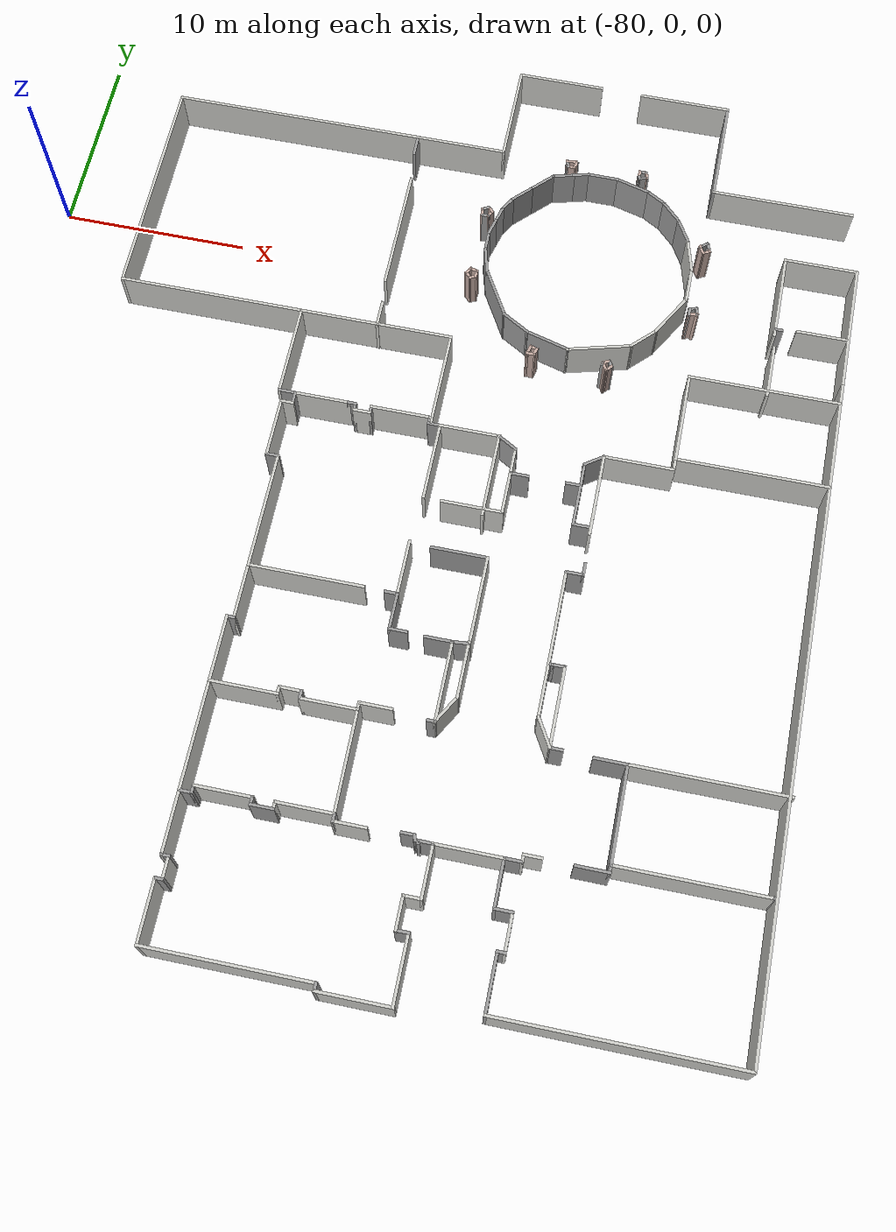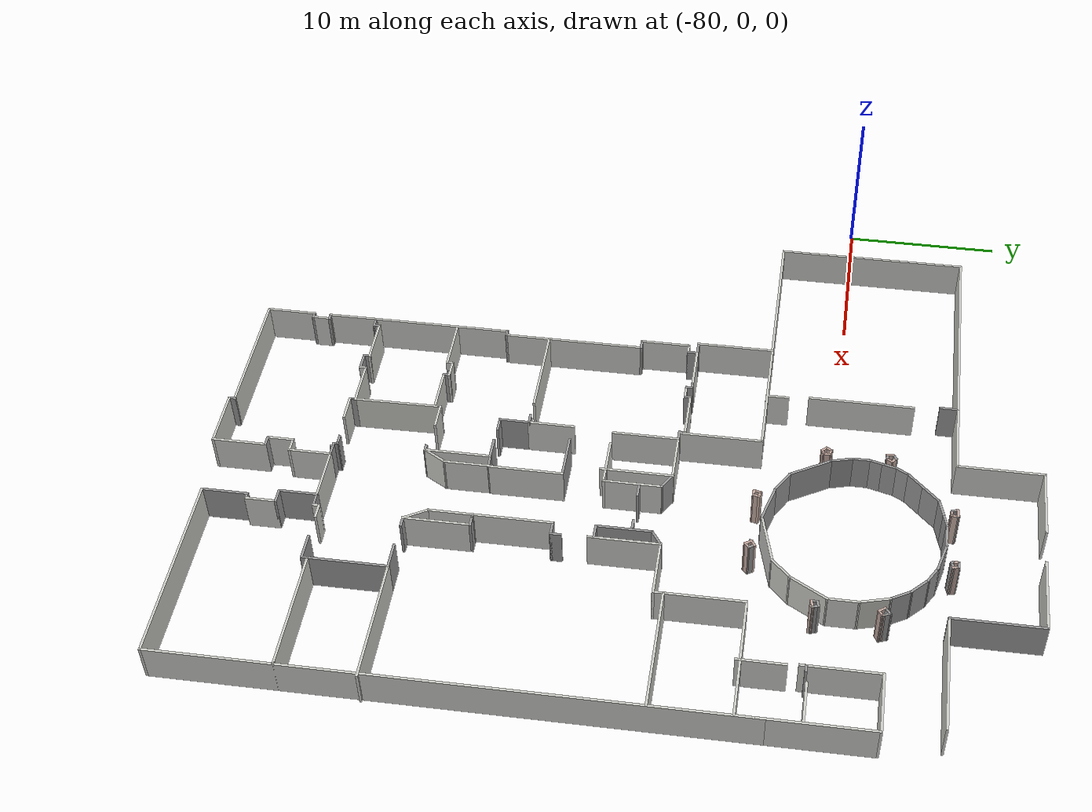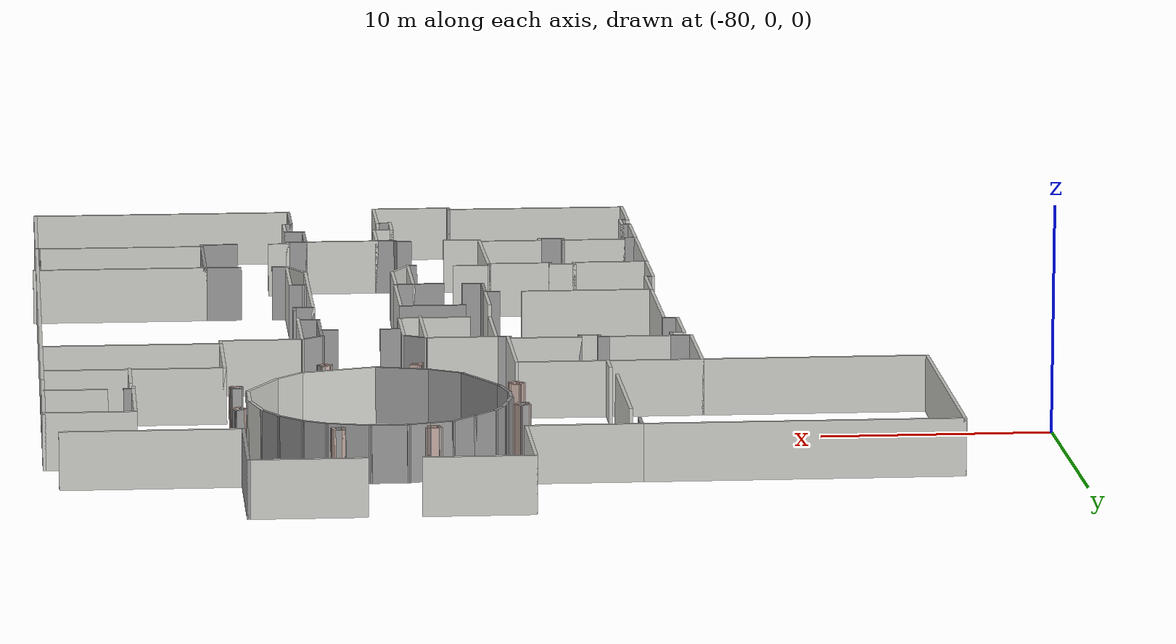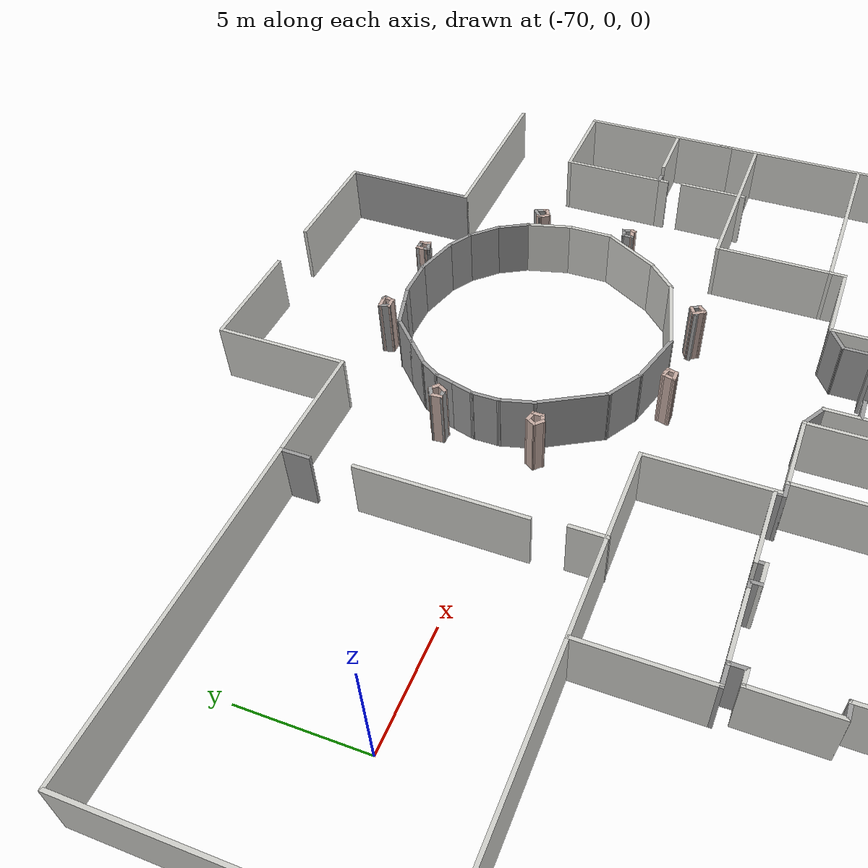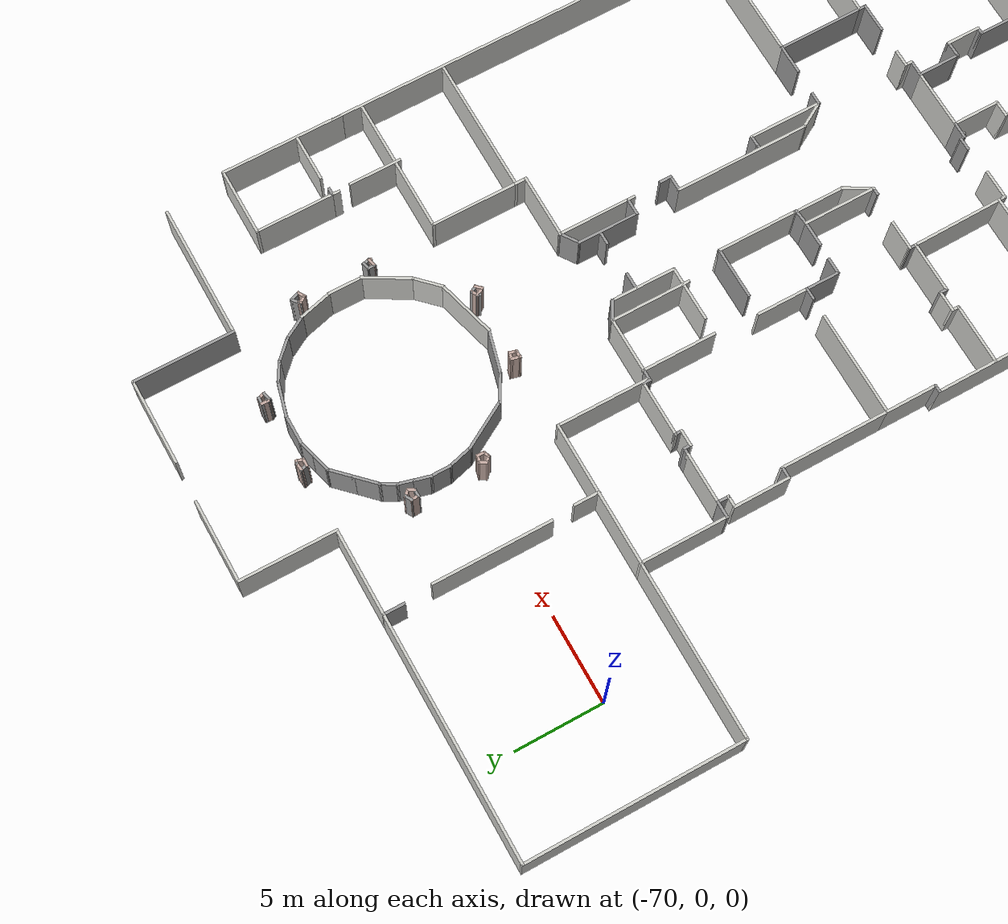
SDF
<?xml version='1.0'?>
<sdf version='1.7'>
  <model name='TD_n1'>
    <pose>-37.6178 -12.8947 0 0 -0 0</pose>
    <link name='Wall_0'>
      <collision name='Wall_0_Collision'>
        <geometry>
          <box>
            <size>35.5 0.15 2.5</size>
          </box>
        </geometry>
        <pose>0 0 1.25 0 -0 0</pose>
      </collision>
      <visual name='Wall_0_Visual'>
        <pose>0 0 1.25 0 -0 0</pose>
        <geometry>
          <box>
            <size>35.5 0.15 2.5</size>
          </box>
        </geometry>
        <material>
          <script>
            <uri>file://media/materials/scripts/gazebo.material</uri>
            <name>Gazebo/CeilingTiled</name>
          </script>
          <ambient>1 1 1 1</ambient>
        </material>
        <meta>
          <layer>0</layer>
        </meta>
      </visual>
      <pose>0.95718 -7.55 0 0 -0 -1.5708</pose>
    </link>
    <link name='Wall_1'>
      <collision name='Wall_1_Collision'>
        <geometry>
          <box>
            <size>12.25 0.15 2.5</size>
          </box>
        </geometry>
        <pose>0 0 1.25 0 -0 0</pose>
      </collision>
      <visual name='Wall_1_Visual'>
        <pose>0 0 1.25 0 -0 0</pose>
        <geometry>
          <box>
            <size>12.25 0.15 2.5</size>
          </box>
        </geometry>
        <material>
          <script>
            <uri>file://media/materials/scripts/gazebo.material</uri>
            <name>Gazebo/CeilingTiled</name>
          </script>
          <ambient>1 1 1 1</ambient>
        </material>
        <meta>
          <layer>0</layer>
        </meta>
      </visual>
      <pose>-5.09282 -25.225 0 0 -0 3.14159</pose>
    </link>
    <link name='Wall_100'>
      <collision name='Wall_100_Collision'>
        <geometry>
          <box>
            <size>6 0.15 2.5</size>
          </box>
        </geometry>
        <pose>0 0 1.25 0 -0 0</pose>
      </collision>
      <visual name='Wall_100_Visual'>
        <pose>0 0 1.25 0 -0 0</pose>
        <geometry>
          <box>
            <size>6 0.15 2.5</size>
          </box>
        </geometry>
        <material>
          <script>
            <uri>file://media/materials/scripts/gazebo.material</uri>
            <name>Gazebo/CeilingTiled</name>
          </script>
          <ambient>1 1 1 1</ambient>
        </material>
        <meta>
          <layer>0</layer>
        </meta>
      </visual>
      <pose>-23.9178 -6.375 0 0 -0 0</pose>
    </link>
    <link name='Wall_102'>
      <collision name='Wall_102_Collision'>
        <geometry>
          <box>
            <size>0.75 0.15 2.5</size>
          </box>
        </geometry>
        <pose>0 0 1.25 0 -0 0</pose>
      </collision>
      <visual name='Wall_102_Visual'>
        <pose>0 0 1.25 0 -0 0</pose>
        <geometry>
          <box>
            <size>0.75 0.15 2.5</size>
          </box>
        </geometry>
        <material>
          <script>
            <uri>file://media/materials/scripts/gazebo.material</uri>
            <name>Gazebo/Grey</name>
          </script>
          <ambient>1 1 1 1</ambient>
        </material>
        <meta>
          <layer>0</layer>
        </meta>
      </visual>
      <pose>-19.5646 -6.4151 0 0 -0 0</pose>
    </link>
    <link name='Wall_103'>
      <collision name='Wall_103_Collision'>
        <geometry>
          <box>
            <size>2 0.15 2.5</size>
          </box>
        </geometry>
        <pose>0 0 1.25 0 -0 0</pose>
      </collision>
      <visual name='Wall_103_Visual'>
        <pose>0 0 1.25 0 -0 0</pose>
        <geometry>
          <box>
            <size>2 0.15 2.5</size>
          </box>
        </geometry>
        <material>
          <script>
            <uri>file://media/materials/scripts/gazebo.material</uri>
            <name>Gazebo/Grey</name>
          </script>
          <ambient>1 1 1 1</ambient>
        </material>
        <meta>
          <layer>0</layer>
        </meta>
      </visual>
      <pose>-19.2646 -7.3401 0 0 -0 -1.5708</pose>
    </link>
    <link name='Wall_104'>
      <collision name='Wall_104_Collision'>
        <geometry>
          <box>
            <size>1 0.15 2.5</size>
          </box>
        </geometry>
        <pose>0 0 1.25 0 -0 0</pose>
      </collision>
      <visual name='Wall_104_Visual'>
        <pose>0 0 1.25 0 -0 0</pose>
        <geometry>
          <box>
            <size>1 0.15 2.5</size>
          </box>
        </geometry>
        <material>
          <script>
            <uri>file://media/materials/scripts/gazebo.material</uri>
            <name>Gazebo/Grey</name>
          </script>
          <ambient>1 1 1 1</ambient>
        </material>
        <meta>
          <layer>0</layer>
        </meta>
      </visual>
      <pose>-18.8396 -8.2651 0 0 -0 0</pose>
    </link>
    <link name='Wall_106'>
      <collision name='Wall_106_Collision'>
        <geometry>
          <box>
            <size>1.5 0.15 2.5</size>
          </box>
        </geometry>
        <pose>0 0 1.25 0 -0 0</pose>
      </collision>
      <visual name='Wall_106_Visual'>
        <pose>0 0 1.25 0 -0 0</pose>
        <geometry>
          <box>
            <size>1.5 0.15 2.5</size>
          </box>
        </geometry>
        <material>
          <script>
            <uri>file://media/materials/scripts/gazebo.material</uri>
            <name>Gazebo/Grey</name>
          </script>
          <ambient>1 1 1 1</ambient>
        </material>
        <meta>
          <layer>0</layer>
        </meta>
      </visual>
      <pose>-16.7826 -8.3195 0 0 -0 0</pose>
    </link>
    <link name='Wall_107'>
      <collision name='Wall_107_Collision'>
        <geometry>
          <box>
            <size>4.25 0.15 2.5</size>
          </box>
        </geometry>
        <pose>0 0 1.25 0 -0 0</pose>
      </collision>
      <visual name='Wall_107_Visual'>
        <pose>0 0 1.25 0 -0 0</pose>
        <geometry>
          <box>
            <size>4.25 0.15 2.5</size>
          </box>
        </geometry>
        <material>
          <script>
            <uri>file://media/materials/scripts/gazebo.material</uri>
            <name>Gazebo/CeilingTiled</name>
          </script>
          <ambient>1 1 1 1</ambient>
        </material>
        <meta>
          <layer>0</layer>
        </meta>
      </visual>
      <pose>-16.1076 -10.3695 0 0 -0 -1.5708</pose>
    </link>
    <link name='Wall_108'>
      <collision name='Wall_108_Collision'>
        <geometry>
          <box>
            <size>0.5 0.15 2.5</size>
          </box>
        </geometry>
        <pose>0 0 1.25 0 -0 0</pose>
      </collision>
      <visual name='Wall_108_Visual'>
        <pose>0 0 1.25 0 -0 0</pose>
        <geometry>
          <box>
            <size>0.5 0.15 2.5</size>
          </box>
        </geometry>
        <material>
          <script>
            <uri>file://media/materials/scripts/gazebo.material</uri>
            <name>Gazebo/Grey</name>
          </script>
          <ambient>1 1 1 1</ambient>
        </material>
        <meta>
          <layer>0</layer>
        </meta>
      </visual>
      <pose>-16.2826 -12.4195 0 0 -0 3.14159</pose>
    </link>
    <link name='Wall_110'>
      <collision name='Wall_110_Collision'>
        <geometry>
          <box>
            <size>3.5 0.15 2.5</size>
          </box>
        </geometry>
        <pose>0 0 1.25 0 -0 0</pose>
      </collision>
      <visual name='Wall_110_Visual'>
        <pose>0 0 1.25 0 -0 0</pose>
        <geometry>
          <box>
            <size>3.5 0.15 2.5</size>
          </box>
        </geometry>
        <material>
          <script>
            <uri>file://media/materials/scripts/gazebo.material</uri>
            <name>Gazebo/CeilingTiled</name>
          </script>
          <ambient>1 1 1 1</ambient>
        </material>
        <meta>
          <layer>0</layer>
        </meta>
      </visual>
      <pose>-25.4898 -12.578 0 0 -0 0</pose>
    </link>
    <link name='Wall_111'>
      <collision name='Wall_111_Collision'>
        <geometry>
          <box>
            <size>0.5 0.15 2.5</size>
          </box>
        </geometry>
        <pose>0 0 1.25 0 -0 0</pose>
      </collision>
      <visual name='Wall_111_Visual'>
        <pose>0 0 1.25 0 -0 0</pose>
        <geometry>
          <box>
            <size>0.5 0.15 2.5</size>
          </box>
        </geometry>
        <material>
          <script>
            <uri>file://media/materials/scripts/gazebo.material</uri>
            <name>Gazebo/CeilingTiled</name>
          </script>
          <ambient>1 1 1 1</ambient>
        </material>
        <meta>
          <layer>0</layer>
        </meta>
      </visual>
      <pose>-23.8148 -12.403 0 0 -0 1.5708</pose>
    </link>
    <link name='Wall_112'>
      <collision name='Wall_112_Collision'>
        <geometry>
          <box>
            <size>1.25 0.15 2.5</size>
          </box>
        </geometry>
        <pose>0 0 1.25 0 -0 0</pose>
      </collision>
      <visual name='Wall_112_Visual'>
        <pose>0 0 1.25 0 -0 0</pose>
        <geometry>
          <box>
            <size>1.25 0.15 2.5</size>
          </box>
        </geometry>
        <material>
          <script>
            <uri>file://media/materials/scripts/gazebo.material</uri>
            <name>Gazebo/CeilingTiled</name>
          </script>
          <ambient>1 1 1 1</ambient>
        </material>
        <meta>
          <layer>0</layer>
        </meta>
      </visual>
      <pose>-23.2648 -12.228 0 0 -0 0</pose>
    </link>
    <link name='Wall_113'>
      <collision name='Wall_113_Collision'>
        <geometry>
          <box>
            <size>0.5 0.15 2.5</size>
          </box>
        </geometry>
        <pose>0 0 1.25 0 -0 0</pose>
      </collision>
      <visual name='Wall_113_Visual'>
        <pose>0 0 1.25 0 -0 0</pose>
        <geometry>
          <box>
            <size>0.5 0.15 2.5</size>
          </box>
        </geometry>
        <material>
          <script>
            <uri>file://media/materials/scripts/gazebo.material</uri>
            <name>Gazebo/Grey</name>
          </script>
          <ambient>1 1 1 1</ambient>
        </material>
        <meta>
          <layer>0</layer>
        </meta>
      </visual>
      <pose>-22.7148 -12.403 0 0 -0 -1.5708</pose>
    </link>
    <link name='Wall_114'>
      <collision name='Wall_114_Collision'>
        <geometry>
          <box>
            <size>3 0.15 2.5</size>
          </box>
        </geometry>
        <pose>0 0 1.25 0 -0 0</pose>
      </collision>
      <visual name='Wall_114_Visual'>
        <pose>0 0 1.25 0 -0 0</pose>
        <geometry>
          <box>
            <size>3 0.15 2.5</size>
          </box>
        </geometry>
        <material>
          <script>
            <uri>file://media/materials/scripts/gazebo.material</uri>
            <name>Gazebo/CeilingTiled</name>
          </script>
          <ambient>1 1 1 1</ambient>
        </material>
        <meta>
          <layer>0</layer>
        </meta>
      </visual>
      <pose>-21.2898 -12.578 0 0 -0 0</pose>
    </link>
    <link name='Wall_115'>
      <collision name='Wall_115_Collision'>
        <geometry>
          <box>
            <size>0.5 0.15 2.5</size>
          </box>
        </geometry>
        <pose>0 0 1.25 0 -0 0</pose>
      </collision>
      <visual name='Wall_115_Visual'>
        <pose>0 0 1.25 0 -0 0</pose>
        <geometry>
          <box>
            <size>0.5 0.15 2.5</size>
          </box>
        </geometry>
        <material>
          <script>
            <uri>file://media/materials/scripts/gazebo.material</uri>
            <name>Gazebo/Grey</name>
          </script>
          <ambient>1 1 1 1</ambient>
        </material>
        <meta>
          <layer>0</layer>
        </meta>
      </visual>
      <pose>-19.8648 -12.403 0 0 -0 1.5708</pose>
    </link>
    <link name='Wall_116'>
      <collision name='Wall_116_Collision'>
        <geometry>
          <box>
            <size>1.75 0.15 2.5</size>
          </box>
        </geometry>
        <pose>0 0 1.25 0 -0 0</pose>
      </collision>
      <visual name='Wall_116_Visual'>
        <pose>0 0 1.25 0 -0 0</pose>
        <geometry>
          <box>
            <size>1.75 0.15 2.5</size>
          </box>
        </geometry>
        <material>
          <script>
            <uri>file://media/materials/scripts/gazebo.material</uri>
            <name>Gazebo/CeilingTiled</name>
          </script>
          <ambient>1 1 1 1</ambient>
        </material>
        <meta>
          <layer>0</layer>
        </meta>
      </visual>
      <pose>-19.0648 -12.228 0 0 -0 0</pose>
    </link>
    <link name='Wall_118'>
      <collision name='Wall_118_Collision'>
        <geometry>
          <box>
            <size>6.25 0.15 2.5</size>
          </box>
        </geometry>
        <pose>0 0 1.25 0 -0 0</pose>
      </collision>
      <visual name='Wall_118_Visual'>
        <pose>0 0 1.25 0 -0 0</pose>
        <geometry>
          <box>
            <size>6.25 0.15 2.5</size>
          </box>
        </geometry>
        <material>
          <script>
            <uri>file://media/materials/scripts/gazebo.material</uri>
            <name>Gazebo/CeilingTiled</name>
          </script>
          <ambient>1 1 1 1</ambient>
        </material>
        <meta>
          <layer>0</layer>
        </meta>
      </visual>
      <pose>-26.8428 -3.325 0 0 -0 1.5708</pose>
    </link>
    <link name='Wall_119'>
      <collision name='Wall_119_Collision'>
        <geometry>
          <box>
            <size>0.75 0.15 2.5</size>
          </box>
        </geometry>
        <pose>0 0 1.25 0 -0 0</pose>
      </collision>
      <visual name='Wall_119_Visual'>
        <pose>0 0 1.25 0 -0 0</pose>
        <geometry>
          <box>
            <size>0.75 0.15 2.5</size>
          </box>
        </geometry>
        <material>
          <script>
            <uri>file://media/materials/scripts/gazebo.material</uri>
            <name>Gazebo/Grey</name>
          </script>
          <ambient>1 1 1 1</ambient>
        </material>
        <meta>
          <layer>0</layer>
        </meta>
      </visual>
      <pose>-27.1428 -0.275001 0 0 -0 3.14159</pose>
    </link>
    <link name='Wall_12'>
      <collision name='Wall_12_Collision'>
        <geometry>
          <box>
            <size>0.5 0.15 2.5</size>
          </box>
        </geometry>
        <pose>0 0 1.25 0 -0 0</pose>
      </collision>
      <visual name='Wall_12_Visual'>
        <pose>0 0 1.25 0 -0 0</pose>
        <geometry>
          <box>
            <size>0.5 0.15 2.5</size>
          </box>
        </geometry>
        <material>
          <script>
            <uri>file://media/materials/scripts/gazebo.material</uri>
            <name>Gazebo/Grey</name>
          </script>
          <ambient>1 1 1 1</ambient>
        </material>
        <meta>
          <layer>0</layer>
        </meta>
      </visual>
      <pose>-10.9678 -22.375 0 0 -0 0</pose>
    </link>
    <link name='Wall_120'>
      <collision name='Wall_120_Collision'>
        <geometry>
          <box>
            <size>3.25 0.15 2.5</size>
          </box>
        </geometry>
        <pose>0 0 1.25 0 -0 0</pose>
      </collision>
      <visual name='Wall_120_Visual'>
        <pose>0 0 1.25 0 -0 0</pose>
        <geometry>
          <box>
            <size>3.25 0.15 2.5</size>
          </box>
        </geometry>
        <material>
          <script>
            <uri>file://media/materials/scripts/gazebo.material</uri>
            <name>Gazebo/CeilingTiled</name>
          </script>
          <ambient>1 1 1 1</ambient>
        </material>
        <meta>
          <layer>0</layer>
        </meta>
      </visual>
      <pose>-27.4428 1.275 0 0 -0 1.5708</pose>
    </link>
    <link name='Wall_121'>
      <collision name='Wall_121_Collision'>
        <geometry>
          <box>
            <size>0.75 0.15 2.5</size>
          </box>
        </geometry>
        <pose>0 0 1.25 0 -0 0</pose>
      </collision>
      <visual name='Wall_121_Visual'>
        <pose>0 0 1.25 0 -0 0</pose>
        <geometry>
          <box>
            <size>0.75 0.15 2.5</size>
          </box>
        </geometry>
        <material>
          <script>
            <uri>file://media/materials/scripts/gazebo.material</uri>
            <name>Gazebo/CeilingTiled</name>
          </script>
          <ambient>1 1 1 1</ambient>
        </material>
        <meta>
          <layer>0</layer>
        </meta>
      </visual>
      <pose>-27.1428 2.825 0 0 -0 0</pose>
    </link>
    <link name='Wall_122'>
      <collision name='Wall_122_Collision'>
        <geometry>
          <box>
            <size>0.75 0.15 2.5</size>
          </box>
        </geometry>
        <pose>0 0 1.25 0 -0 0</pose>
      </collision>
      <visual name='Wall_122_Visual'>
        <pose>0 0 1.25 0 -0 0</pose>
        <geometry>
          <box>
            <size>0.75 0.15 2.5</size>
          </box>
        </geometry>
        <material>
          <script>
            <uri>file://media/materials/scripts/gazebo.material</uri>
            <name>Gazebo/Grey</name>
          </script>
          <ambient>1 1 1 1</ambient>
        </material>
        <meta>
          <layer>0</layer>
        </meta>
      </visual>
      <pose>-26.8428 3.125 0 0 -0 1.5708</pose>
    </link>
    <link name='Wall_123'>
      <collision name='Wall_123_Collision'>
        <geometry>
          <box>
            <size>3 0.15 2.5</size>
          </box>
        </geometry>
        <pose>0 0 1.25 0 -0 0</pose>
      </collision>
      <visual name='Wall_123_Visual'>
        <pose>0 0 1.25 0 -0 0</pose>
        <geometry>
          <box>
            <size>3 0.15 2.5</size>
          </box>
        </geometry>
        <material>
          <script>
            <uri>file://media/materials/scripts/gazebo.material</uri>
            <name>Gazebo/CeilingTiled</name>
          </script>
          <ambient>1 1 1 1</ambient>
        </material>
        <meta>
          <layer>0</layer>
        </meta>
      </visual>
      <pose>-25.4178 3.425 0 0 -0 0</pose>
    </link>
    <link name='Wall_125'>
      <collision name='Wall_125_Collision'>
        <geometry>
          <box>
            <size>0.5 0.15 2.5</size>
          </box>
        </geometry>
        <pose>0 0 1.25 0 -0 0</pose>
      </collision>
      <visual name='Wall_125_Visual'>
        <pose>0 0 1.25 0 -0 0</pose>
        <geometry>
          <box>
            <size>0.5 0.15 2.5</size>
          </box>
        </geometry>
        <material>
          <script>
            <uri>file://media/materials/scripts/gazebo.material</uri>
            <name>Gazebo/Grey</name>
          </script>
          <ambient>1 1 1 1</ambient>
        </material>
        <meta>
          <layer>0</layer>
        </meta>
      </visual>
      <pose>-23.8178 3.425 0 0 -0 0</pose>
    </link>
    <link name='Wall_126'>
      <collision name='Wall_126_Collision'>
        <geometry>
          <box>
            <size>0.5 0.15 2.5</size>
          </box>
        </geometry>
        <pose>0 0 1.25 0 -0 0</pose>
      </collision>
      <visual name='Wall_126_Visual'>
        <pose>0 0 1.25 0 -0 0</pose>
        <geometry>
          <box>
            <size>0.5 0.15 2.5</size>
          </box>
        </geometry>
        <material>
          <script>
            <uri>file://media/materials/scripts/gazebo.material</uri>
            <name>Gazebo/Grey</name>
          </script>
          <ambient>1 1 1 1</ambient>
        </material>
        <meta>
          <layer>0</layer>
        </meta>
      </visual>
      <pose>-23.6428 3.25 0 0 -0 -1.5708</pose>
    </link>
    <link name='Wall_127'>
      <collision name='Wall_127_Collision'>
        <geometry>
          <box>
            <size>1 0.15 2.5</size>
          </box>
        </geometry>
        <pose>0 0 1.25 0 -0 0</pose>
      </collision>
      <visual name='Wall_127_Visual'>
        <pose>0 0 1.25 0 -0 0</pose>
        <geometry>
          <box>
            <size>1 0.15 2.5</size>
          </box>
        </geometry>
        <material>
          <script>
            <uri>file://media/materials/scripts/gazebo.material</uri>
            <name>Gazebo/CeilingTiled</name>
          </script>
          <ambient>1 1 1 1</ambient>
        </material>
        <meta>
          <layer>0</layer>
        </meta>
      </visual>
      <pose>-23.2178 3.075 0 0 -0 0</pose>
    </link>
    <link name='Wall_128'>
      <collision name='Wall_128_Collision'>
        <geometry>
          <box>
            <size>0.5 0.15 2.5</size>
          </box>
        </geometry>
        <pose>0 0 1.25 0 -0 0</pose>
      </collision>
      <visual name='Wall_128_Visual'>
        <pose>0 0 1.25 0 -0 0</pose>
        <geometry>
          <box>
            <size>0.5 0.15 2.5</size>
          </box>
        </geometry>
        <material>
          <script>
            <uri>file://media/materials/scripts/gazebo.material</uri>
            <name>Gazebo/Grey</name>
          </script>
          <ambient>1 1 1 1</ambient>
        </material>
        <meta>
          <layer>0</layer>
        </meta>
      </visual>
      <pose>-22.7928 3.25 0 0 -0 1.5708</pose>
    </link>
    <link name='Wall_129'>
      <collision name='Wall_129_Collision'>
        <geometry>
          <box>
            <size>3.25 0.15 2.5</size>
          </box>
        </geometry>
        <pose>0 0 1.25 0 -0 0</pose>
      </collision>
      <visual name='Wall_129_Visual'>
        <pose>0 0 1.25 0 -0 0</pose>
        <geometry>
          <box>
            <size>3.25 0.15 2.5</size>
          </box>
        </geometry>
        <material>
          <script>
            <uri>file://media/materials/scripts/gazebo.material</uri>
            <name>Gazebo/CeilingTiled</name>
          </script>
          <ambient>1 1 1 1</ambient>
        </material>
        <meta>
          <layer>0</layer>
        </meta>
      </visual>
      <pose>-21.2428 3.425 0 0 -0 0</pose>
    </link>
    <link name='Wall_13'>
      <collision name='Wall_13_Collision'>
        <geometry>
          <box>
            <size>2 0.15 2.5</size>
          </box>
        </geometry>
        <pose>0 0 1.25 0 -0 0</pose>
      </collision>
      <visual name='Wall_13_Visual'>
        <pose>0 0 1.25 0 -0 0</pose>
        <geometry>
          <box>
            <size>2 0.15 2.5</size>
          </box>
        </geometry>
        <material>
          <script>
            <uri>file://media/materials/scripts/gazebo.material</uri>
            <name>Gazebo/CeilingTiled</name>
          </script>
          <ambient>1 1 1 1</ambient>
        </material>
        <meta>
          <layer>0</layer>
        </meta>
      </visual>
      <pose>-10.7928 -21.45 0 0 -0 1.5708</pose>
    </link>
    <link name='Wall_130'>
      <collision name='Wall_130_Collision'>
        <geometry>
          <box>
            <size>0.5 0.15 2.5</size>
          </box>
        </geometry>
        <pose>0 0 1.25 0 -0 0</pose>
      </collision>
      <visual name='Wall_130_Visual'>
        <pose>0 0 1.25 0 -0 0</pose>
        <geometry>
          <box>
            <size>0.5 0.15 2.5</size>
          </box>
        </geometry>
        <material>
          <script>
            <uri>file://media/materials/scripts/gazebo.material</uri>
            <name>Gazebo/Grey</name>
          </script>
          <ambient>1 1 1 1</ambient>
        </material>
        <meta>
          <layer>0</layer>
        </meta>
      </visual>
      <pose>-19.6928 3.25 0 0 -0 -1.5708</pose>
    </link>
    <link name='Wall_131'>
      <collision name='Wall_131_Collision'>
        <geometry>
          <box>
            <size>0.75 0.15 2.5</size>
          </box>
        </geometry>
        <pose>0 0 1.25 0 -0 0</pose>
      </collision>
      <visual name='Wall_131_Visual'>
        <pose>0 0 1.25 0 -0 0</pose>
        <geometry>
          <box>
            <size>0.75 0.15 2.5</size>
          </box>
        </geometry>
        <material>
          <script>
            <uri>file://media/materials/scripts/gazebo.material</uri>
            <name>Gazebo/Grey</name>
          </script>
          <ambient>1 1 1 1</ambient>
        </material>
        <meta>
          <layer>0</layer>
        </meta>
      </visual>
      <pose>-19.3928 3.075 0 0 -0 0</pose>
    </link>
    <link name='Wall_132'>
      <collision name='Wall_132_Collision'>
        <geometry>
          <box>
            <size>4.25 0.15 2.5</size>
          </box>
        </geometry>
        <pose>0 0 1.25 0 -0 0</pose>
      </collision>
      <visual name='Wall_132_Visual'>
        <pose>0 0 1.25 0 -0 0</pose>
        <geometry>
          <box>
            <size>4.25 0.15 2.5</size>
          </box>
        </geometry>
        <material>
          <script>
            <uri>file://media/materials/scripts/gazebo.material</uri>
            <name>Gazebo/CeilingTiled</name>
          </script>
          <ambient>1 1 1 1</ambient>
        </material>
        <meta>
          <layer>0</layer>
        </meta>
      </visual>
      <pose>-19.0928 1.025 0 0 -0 -1.5708</pose>
    </link>
    <link name='Wall_134'>
      <collision name='Wall_134_Collision'>
        <geometry>
          <box>
            <size>3.25 0.15 2.5</size>
          </box>
        </geometry>
        <pose>0 0 1.25 0 -0 0</pose>
      </collision>
      <visual name='Wall_134_Visual'>
        <pose>0 0 1.25 0 -0 0</pose>
        <geometry>
          <box>
            <size>3.25 0.15 2.5</size>
          </box>
        </geometry>
        <material>
          <script>
            <uri>file://media/materials/scripts/gazebo.material</uri>
            <name>Gazebo/CeilingTiled</name>
          </script>
          <ambient>1 1 1 1</ambient>
        </material>
        <meta>
          <layer>0</layer>
        </meta>
      </visual>
      <pose>-17.5428 3.075 0 0 -0 0</pose>
    </link>
    <link name='Wall_135'>
      <collision name='Wall_135_Collision'>
        <geometry>
          <box>
            <size>1.25 0.15 2.5</size>
          </box>
        </geometry>
        <pose>0 0 1.25 0 -0 0</pose>
      </collision>
      <visual name='Wall_135_Visual'>
        <pose>0 0 1.25 0 -0 0</pose>
        <geometry>
          <box>
            <size>1.25 0.15 2.5</size>
          </box>
        </geometry>
        <material>
          <script>
            <uri>file://media/materials/scripts/gazebo.material</uri>
            <name>Gazebo/Grey</name>
          </script>
          <ambient>1 1 1 1</ambient>
        </material>
        <meta>
          <layer>0</layer>
        </meta>
      </visual>
      <pose>-15.5165 2.8 0 0 -0 -0.523599</pose>
    </link>
    <link name='Wall_136'>
      <collision name='Wall_136_Collision'>
        <geometry>
          <box>
            <size>3.75 0.15 2.5</size>
          </box>
        </geometry>
        <pose>0 0 1.25 0 -0 0</pose>
      </collision>
      <visual name='Wall_136_Visual'>
        <pose>0 0 1.25 0 -0 0</pose>
        <geometry>
          <box>
            <size>3.75 0.15 2.5</size>
          </box>
        </geometry>
        <material>
          <script>
            <uri>file://media/materials/scripts/gazebo.material</uri>
            <name>Gazebo/CeilingTiled</name>
          </script>
          <ambient>1 1 1 1</ambient>
        </material>
        <meta>
          <layer>0</layer>
        </meta>
      </visual>
      <pose>-15.0402 0.724999 0 0 -0 -1.5708</pose>
    </link>
    <link name='Wall_137'>
      <collision name='Wall_137_Collision'>
        <geometry>
          <box>
            <size>3.25 0.15 2.5</size>
          </box>
        </geometry>
        <pose>0 0 1.25 0 -0 0</pose>
      </collision>
      <visual name='Wall_137_Visual'>
        <pose>0 0 1.25 0 -0 0</pose>
        <geometry>
          <box>
            <size>3.25 0.15 2.5</size>
          </box>
        </geometry>
        <material>
          <script>
            <uri>file://media/materials/scripts/gazebo.material</uri>
            <name>Gazebo/CeilingTiled</name>
          </script>
          <ambient>1 1 1 1</ambient>
        </material>
        <meta>
          <layer>0</layer>
        </meta>
      </visual>
      <pose>-16.5902 -1.075 0 0 -0 3.14159</pose>
    </link>
    <link name='Wall_139'>
      <collision name='Wall_139_Collision'>
        <geometry>
          <box>
            <size>4.25 0.15 2.5</size>
          </box>
        </geometry>
        <pose>0 0 1.25 0 -0 0</pose>
      </collision>
      <visual name='Wall_139_Visual'>
        <pose>0 0 1.25 0 -0 0</pose>
        <geometry>
          <box>
            <size>4.25 0.15 2.5</size>
          </box>
        </geometry>
        <material>
          <script>
            <uri>file://media/materials/scripts/gazebo.material</uri>
            <name>Gazebo/CeilingTiled</name>
          </script>
          <ambient>1 1 1 1</ambient>
        </material>
        <meta>
          <layer>0</layer>
        </meta>
      </visual>
      <pose>-15.9928 1.025 0 0 -0 -1.5708</pose>
    </link>
    <link name='Wall_14'>
      <collision name='Wall_14_Collision'>
        <geometry>
          <box>
            <size>1 0.15 2.5</size>
          </box>
        </geometry>
        <pose>0 0 1.25 0 -0 0</pose>
      </collision>
      <visual name='Wall_14_Visual'>
        <pose>0 0 1.25 0 -0 0</pose>
        <geometry>
          <box>
            <size>1 0.15 2.5</size>
          </box>
        </geometry>
        <material>
          <script>
            <uri>file://media/materials/scripts/gazebo.material</uri>
            <name>Gazebo/Grey</name>
          </script>
          <ambient>1 1 1 1</ambient>
        </material>
        <meta>
          <layer>0</layer>
        </meta>
      </visual>
      <pose>-11.2178 -20.525 0 0 -0 3.14159</pose>
    </link>
    <link name='Wall_140'>
      <collision name='Wall_140_Collision'>
        <geometry>
          <box>
            <size>0.5 0.15 2.5</size>
          </box>
        </geometry>
        <pose>0 0 1.25 0 -0 0</pose>
      </collision>
      <visual name='Wall_140_Visual'>
        <pose>0 0 1.25 0 -0 0</pose>
        <geometry>
          <box>
            <size>0.5 0.15 2.5</size>
          </box>
        </geometry>
        <material>
          <script>
            <uri>file://media/materials/scripts/gazebo.material</uri>
            <name>Gazebo/CeilingTiled</name>
          </script>
          <ambient>1 1 1 1</ambient>
        </material>
        <meta>
          <layer>0</layer>
        </meta>
      </visual>
      <pose>-15.9928 -1.2 0 0 -0 -1.5708</pose>
    </link>
    <link name='Wall_142'>
      <collision name='Wall_142_Collision'>
        <geometry>
          <box>
            <size>3 0.15 2.5</size>
          </box>
        </geometry>
        <pose>0 0 1.25 0 -0 0</pose>
      </collision>
      <visual name='Wall_142_Visual'>
        <pose>0 0 1.25 0 -0 0</pose>
        <geometry>
          <box>
            <size>3 0.15 2.5</size>
          </box>
        </geometry>
        <material>
          <script>
            <uri>file://media/materials/scripts/gazebo.material</uri>
            <name>Gazebo/CeilingTiled</name>
          </script>
          <ambient>1 1 1 1</ambient>
        </material>
        <meta>
          <layer>0</layer>
        </meta>
      </visual>
      <pose>-19.2646 -4.9901 0 0 -0 1.5708</pose>
    </link>
    <link name='Wall_145'>
      <collision name='Wall_145_Collision'>
        <geometry>
          <box>
            <size>3 0.15 2.5</size>
          </box>
        </geometry>
        <pose>0 0 1.25 0 -0 0</pose>
      </collision>
      <visual name='Wall_145_Visual'>
        <pose>0 0 1.25 0 -0 0</pose>
        <geometry>
          <box>
            <size>3 0.15 2.5</size>
          </box>
        </geometry>
        <material>
          <script>
            <uri>file://media/materials/scripts/gazebo.material</uri>
            <name>Gazebo/Grey</name>
          </script>
          <ambient>1 1 1 1</ambient>
        </material>
        <meta>
          <layer>0</layer>
        </meta>
      </visual>
      <pose>-16.6986 -3.64843 0 0 -0 0</pose>
    </link>
    <link name='Wall_146'>
      <collision name='Wall_146_Collision'>
        <geometry>
          <box>
            <size>4.75 0.15 2.5</size>
          </box>
        </geometry>
        <pose>0 0 1.25 0 -0 0</pose>
      </collision>
      <visual name='Wall_146_Visual'>
        <pose>0 0 1.25 0 -0 0</pose>
        <geometry>
          <box>
            <size>4.75 0.15 2.5</size>
          </box>
        </geometry>
        <material>
          <script>
            <uri>file://media/materials/scripts/gazebo.material</uri>
            <name>Gazebo/CeilingTiled</name>
          </script>
          <ambient>1 1 1 1</ambient>
        </material>
        <meta>
          <layer>0</layer>
        </meta>
      </visual>
      <pose>-15.2736 -5.94843 0 0 -0 -1.5708</pose>
    </link>
    <link name='Wall_147'>
      <collision name='Wall_147_Collision'>
        <geometry>
          <box>
            <size>0.987042 0.15 2.5</size>
          </box>
        </geometry>
        <pose>0 0 1.25 0 -0 0</pose>
      </collision>
      <visual name='Wall_147_Visual'>
        <pose>0 0 1.25 0 -0 0</pose>
        <geometry>
          <box>
            <size>0.987042 0.15 2.5</size>
          </box>
        </geometry>
        <material>
          <script>
            <uri>file://media/materials/scripts/gazebo.material</uri>
            <name>Gazebo/Grey</name>
          </script>
          <ambient>1 1 1 1</ambient>
        </material>
        <meta>
          <layer>0</layer>
        </meta>
      </visual>
      <pose>-15.6906 -8.28397 0 0 -0 -3.05658</pose>
    </link>
    <link name='Wall_15'>
      <collision name='Wall_15_Collision'>
        <geometry>
          <box>
            <size>2.5 0.15 2.5</size>
          </box>
        </geometry>
        <pose>0 0 1.25 0 -0 0</pose>
      </collision>
      <visual name='Wall_15_Visual'>
        <pose>0 0 1.25 0 -0 0</pose>
        <geometry>
          <box>
            <size>2.5 0.15 2.5</size>
          </box>
        </geometry>
        <material>
          <script>
            <uri>file://media/materials/scripts/gazebo.material</uri>
            <name>Gazebo/Grey</name>
          </script>
          <ambient>1 1 1 1</ambient>
        </material>
        <meta>
          <layer>0</layer>
        </meta>
      </visual>
      <pose>-11.6428 -19.35 0 0 -0 1.5708</pose>
    </link>
    <link name='Wall_152'>
      <collision name='Wall_152_Collision'>
        <geometry>
          <box>
            <size>1.75 0.15 2.5</size>
          </box>
        </geometry>
        <pose>0 0 1.25 0 -0 0</pose>
      </collision>
      <visual name='Wall_152_Visual'>
        <pose>0 0 1.25 0 -0 0</pose>
        <geometry>
          <box>
            <size>1.75 0.15 2.5</size>
          </box>
        </geometry>
        <material>
          <script>
            <uri>file://media/materials/scripts/gazebo.material</uri>
            <name>Gazebo/CeilingTiled</name>
          </script>
          <ambient>1 1 1 1</ambient>
        </material>
        <meta>
          <layer>0</layer>
        </meta>
      </visual>
      <pose>-15.7076 -11.7267 0 0 -0 1.0472</pose>
    </link>
    <link name='Wall_153'>
      <collision name='Wall_153_Collision'>
        <geometry>
          <box>
            <size>3 0.15 2.5</size>
          </box>
        </geometry>
        <pose>0 0 1.25 0 -0 0</pose>
      </collision>
      <visual name='Wall_153_Visual'>
        <pose>0 0 1.25 0 -0 0</pose>
        <geometry>
          <box>
            <size>3 0.15 2.5</size>
          </box>
        </geometry>
        <material>
          <script>
            <uri>file://media/materials/scripts/gazebo.material</uri>
            <name>Gazebo/CeilingTiled</name>
          </script>
          <ambient>1 1 1 1</ambient>
        </material>
        <meta>
          <layer>0</layer>
        </meta>
      </visual>
      <pose>-15.3076 -9.60886 0 0 -0 1.5708</pose>
    </link>
    <link name='Wall_155'>
      <collision name='Wall_155_Collision'>
        <geometry>
          <box>
            <size>0.25 0.15 2.5</size>
          </box>
        </geometry>
        <pose>0 0 1.25 0 -0 0</pose>
      </collision>
      <visual name='Wall_155_Visual'>
        <pose>0 0 1.25 0 -0 0</pose>
        <geometry>
          <box>
            <size>0.25 0.15 2.5</size>
          </box>
        </geometry>
        <material>
          <script>
            <uri>file://media/materials/scripts/gazebo.material</uri>
            <name>Gazebo/Grey</name>
          </script>
          <ambient>1 1 1 1</ambient>
        </material>
        <meta>
          <layer>0</layer>
        </meta>
      </visual>
      <pose>-11.1638 -8.48796 0 0 -0 3.14159</pose>
    </link>
    <link name='Wall_157'>
      <collision name='Wall_157_Collision'>
        <geometry>
          <box>
            <size>1 0.15 2.5</size>
          </box>
        </geometry>
        <pose>0 0 1.25 0 -0 0</pose>
      </collision>
      <visual name='Wall_157_Visual'>
        <pose>0 0 1.25 0 -0 0</pose>
        <geometry>
          <box>
            <size>1 0.15 2.5</size>
          </box>
        </geometry>
        <material>
          <script>
            <uri>file://media/materials/scripts/gazebo.material</uri>
            <name>Gazebo/Grey</name>
          </script>
          <ambient>1 1 1 1</ambient>
        </material>
        <meta>
          <layer>0</layer>
        </meta>
      </visual>
      <pose>-10.9975 -1.00817 0 0 -0 0</pose>
    </link>
    <link name='Wall_159'>
      <collision name='Wall_159_Collision'>
        <geometry>
          <box>
            <size>3.54074 0.15 2.5</size>
          </box>
        </geometry>
        <pose>0 0 1.25 0 -0 0</pose>
      </collision>
      <visual name='Wall_159_Visual'>
        <pose>0 0 1.25 0 -0 0</pose>
        <geometry>
          <box>
            <size>3.54074 0.15 2.5</size>
          </box>
        </geometry>
        <material>
          <script>
            <uri>file://media/materials/scripts/gazebo.material</uri>
            <name>Gazebo/Grey</name>
          </script>
          <ambient>1 1 1 1</ambient>
        </material>
        <meta>
          <layer>0</layer>
        </meta>
      </visual>
      <pose>-11.4225 0.687201 0 0 -0 -1.5708</pose>
    </link>
    <link name='Wall_16'>
      <collision name='Wall_16_Collision'>
        <geometry>
          <box>
            <size>1 0.15 2.5</size>
          </box>
        </geometry>
        <pose>0 0 1.25 0 -0 0</pose>
      </collision>
      <visual name='Wall_16_Visual'>
        <pose>0 0 1.25 0 -0 0</pose>
        <geometry>
          <box>
            <size>1 0.15 2.5</size>
          </box>
        </geometry>
        <material>
          <script>
            <uri>file://media/materials/scripts/gazebo.material</uri>
            <name>Gazebo/Grey</name>
          </script>
          <ambient>1 1 1 1</ambient>
        </material>
        <meta>
          <layer>0</layer>
        </meta>
      </visual>
      <pose>-11.2178 -18.175 0 0 -0 0</pose>
    </link>
    <link name='Wall_161'>
      <collision name='Wall_161_Collision'>
        <geometry>
          <box>
            <size>1.23577 0.15 2.5</size>
          </box>
        </geometry>
        <pose>0 0 1.25 0 -0 0</pose>
      </collision>
      <visual name='Wall_161_Visual'>
        <pose>0 0 1.25 0 -0 0</pose>
        <geometry>
          <box>
            <size>1.23577 0.15 2.5</size>
          </box>
        </geometry>
        <material>
          <script>
            <uri>file://media/materials/scripts/gazebo.material</uri>
            <name>Gazebo/Grey</name>
          </script>
          <ambient>1 1 1 1</ambient>
        </material>
        <meta>
          <layer>0</layer>
        </meta>
      </visual>
      <pose>-10.9749 2.68981 0 0 -0 0.601557</pose>
    </link>
    <link name='Wall_163'>
      <collision name='Wall_163_Collision'>
        <geometry>
          <box>
            <size>5.99749 0.15 2.5</size>
          </box>
        </geometry>
        <pose>0 0 1.25 0 -0 0</pose>
      </collision>
      <visual name='Wall_163_Visual'>
        <pose>0 0 1.25 0 -0 0</pose>
        <geometry>
          <box>
            <size>5.99749 0.15 2.5</size>
          </box>
        </geometry>
        <material>
          <script>
            <uri>file://media/materials/scripts/gazebo.material</uri>
            <name>Gazebo/CeilingTiled</name>
          </script>
          <ambient>1 1 1 1</ambient>
        </material>
        <meta>
          <layer>0</layer>
        </meta>
      </visual>
      <pose>-19.8288 -15.1515 0 0 -0 1.5831</pose>
    </link>
    <link name='Wall_165'>
      <collision name='Wall_165_Collision'>
        <geometry>
          <box>
            <size>1 0.15 2.5</size>
          </box>
        </geometry>
        <pose>0 0 1.25 0 -0 0</pose>
      </collision>
      <visual name='Wall_165_Visual'>
        <pose>0 0 1.25 0 -0 0</pose>
        <geometry>
          <box>
            <size>1 0.15 2.5</size>
          </box>
        </geometry>
        <material>
          <script>
            <uri>file://media/materials/scripts/gazebo.material</uri>
            <name>Gazebo/Grey</name>
          </script>
          <ambient>1 1 1 1</ambient>
        </material>
        <meta>
          <layer>0</layer>
        </meta>
      </visual>
      <pose>-27.2678 3.425 0 0 -0 3.14159</pose>
    </link>
    <link name='Wall_166'>
      <collision name='Wall_166_Collision'>
        <geometry>
          <box>
            <size>5 0.15 2.5</size>
          </box>
        </geometry>
        <pose>0 0 1.25 0 -0 0</pose>
      </collision>
      <visual name='Wall_166_Visual'>
        <pose>0 0 1.25 0 -0 0</pose>
        <geometry>
          <box>
            <size>5 0.15 2.5</size>
          </box>
        </geometry>
        <material>
          <script>
            <uri>file://media/materials/scripts/gazebo.material</uri>
            <name>Gazebo/CeilingTiled</name>
          </script>
          <ambient>1 1 1 1</ambient>
        </material>
        <meta>
          <layer>0</layer>
        </meta>
      </visual>
      <pose>-27.6928 5.85 0 0 -0 1.5708</pose>
    </link>
    <link name='Wall_167'>
      <collision name='Wall_167_Collision'>
        <geometry>
          <box>
            <size>8.25 0.15 2.5</size>
          </box>
        </geometry>
        <pose>0 0 1.25 0 -0 0</pose>
      </collision>
      <visual name='Wall_167_Visual'>
        <pose>0 0 1.25 0 -0 0</pose>
        <geometry>
          <box>
            <size>8.25 0.15 2.5</size>
          </box>
        </geometry>
        <material>
          <script>
            <uri>file://media/materials/scripts/gazebo.material</uri>
            <name>Gazebo/CeilingTiled</name>
          </script>
          <ambient>1 1 1 1</ambient>
        </material>
        <meta>
          <layer>0</layer>
        </meta>
      </visual>
      <pose>-23.6428 8.275 0 0 -0 0</pose>
    </link>
    <link name='Wall_168'>
      <collision name='Wall_168_Collision'>
        <geometry>
          <box>
            <size>5.25 0.15 2.5</size>
          </box>
        </geometry>
        <pose>0 0 1.25 0 -0 0</pose>
      </collision>
      <visual name='Wall_168_Visual'>
        <pose>0 0 1.25 0 -0 0</pose>
        <geometry>
          <box>
            <size>5.25 0.15 2.5</size>
          </box>
        </geometry>
        <material>
          <script>
            <uri>file://media/materials/scripts/gazebo.material</uri>
            <name>Gazebo/CeilingTiled</name>
          </script>
          <ambient>1 1 1 1</ambient>
        </material>
        <meta>
          <layer>0</layer>
        </meta>
      </visual>
      <pose>-19.5928 5.725 0 0 -0 -1.5708</pose>
    </link>
    <link name='Wall_17'>
      <collision name='Wall_17_Collision'>
        <geometry>
          <box>
            <size>0.5 0.15 2.5</size>
          </box>
        </geometry>
        <pose>0 0 1.25 0 -0 0</pose>
      </collision>
      <visual name='Wall_17_Visual'>
        <pose>0 0 1.25 0 -0 0</pose>
        <geometry>
          <box>
            <size>0.5 0.15 2.5</size>
          </box>
        </geometry>
        <material>
          <script>
            <uri>file://media/materials/scripts/gazebo.material</uri>
            <name>Gazebo/CeilingTiled</name>
          </script>
          <ambient>1 1 1 1</ambient>
        </material>
        <meta>
          <layer>0</layer>
        </meta>
      </visual>
      <pose>-10.7928 -18 0 0 -0 1.5708</pose>
    </link>
    <link name='Wall_170'>
      <collision name='Wall_170_Collision'>
        <geometry>
          <box>
            <size>10 0.15 2.5</size>
          </box>
        </geometry>
        <pose>0 0 1.25 0 -0 0</pose>
      </collision>
      <visual name='Wall_170_Visual'>
        <pose>0 0 1.25 0 -0 0</pose>
        <geometry>
          <box>
            <size>10 0.15 2.5</size>
          </box>
        </geometry>
        <material>
          <script>
            <uri>file://media/materials/scripts/gazebo.material</uri>
            <name>Gazebo/CeilingTiled</name>
          </script>
          <ambient>1 1 1 1</ambient>
        </material>
        <meta>
          <layer>0</layer>
        </meta>
      </visual>
      <pose>-32.6178 8.275 0 0 -0 3.14159</pose>
    </link>
    <link name='Wall_171'>
      <collision name='Wall_171_Collision'>
        <geometry>
          <box>
            <size>12.25 0.15 2.5</size>
          </box>
        </geometry>
        <pose>0 0 1.25 0 -0 0</pose>
      </collision>
      <visual name='Wall_171_Visual'>
        <pose>0 0 1.25 0 -0 0</pose>
        <geometry>
          <box>
            <size>12.25 0.15 2.5</size>
          </box>
        </geometry>
        <material>
          <script>
            <uri>file://media/materials/scripts/gazebo.material</uri>
            <name>Gazebo/CeilingTiled</name>
          </script>
          <ambient>1 1 1 1</ambient>
        </material>
        <meta>
          <layer>0</layer>
        </meta>
      </visual>
      <pose>-37.5428 14.325 0 0 -0 1.5708</pose>
    </link>
    <link name='Wall_172'>
      <collision name='Wall_172_Collision'>
        <geometry>
          <box>
            <size>13.75 0.15 2.5</size>
          </box>
        </geometry>
        <pose>0 0 1.25 0 -0 0</pose>
      </collision>
      <visual name='Wall_172_Visual'>
        <pose>0 0 1.25 0 -0 0</pose>
        <geometry>
          <box>
            <size>13.75 0.15 2.5</size>
          </box>
        </geometry>
        <material>
          <script>
            <uri>file://media/materials/scripts/gazebo.material</uri>
            <name>Gazebo/CeilingTiled</name>
          </script>
          <ambient>1 1 1 1</ambient>
        </material>
        <meta>
          <layer>0</layer>
        </meta>
      </visual>
      <pose>-30.7428 20.375 0 0 -0 0</pose>
    </link>
    <link name='Wall_173'>
      <collision name='Wall_173_Collision'>
        <geometry>
          <box>
            <size>1.25 0.15 2.5</size>
          </box>
        </geometry>
        <pose>0 0 1.25 0 -0 0</pose>
      </collision>
      <visual name='Wall_173_Visual'>
        <pose>0 0 1.25 0 -0 0</pose>
        <geometry>
          <box>
            <size>1.25 0.15 2.5</size>
          </box>
        </geometry>
        <material>
          <script>
            <uri>file://media/materials/scripts/gazebo.material</uri>
            <name>Gazebo/Grey</name>
          </script>
          <ambient>1 1 1 1</ambient>
        </material>
        <meta>
          <layer>0</layer>
        </meta>
      </visual>
      <pose>-23.9428 19.825 0 0 -0 -1.5708</pose>
    </link>
    <link name='Wall_175'>
      <collision name='Wall_175_Collision'>
        <geometry>
          <box>
            <size>6.75 0.15 2.5</size>
          </box>
        </geometry>
        <pose>0 0 1.25 0 -0 0</pose>
      </collision>
      <visual name='Wall_175_Visual'>
        <pose>0 0 1.25 0 -0 0</pose>
        <geometry>
          <box>
            <size>6.75 0.15 2.5</size>
          </box>
        </geometry>
        <material>
          <script>
            <uri>file://media/materials/scripts/gazebo.material</uri>
            <name>Gazebo/CeilingTiled</name>
          </script>
          <ambient>1 1 1 1</ambient>
        </material>
        <meta>
          <layer>0</layer>
        </meta>
      </visual>
      <pose>-23.7341 14.2836 0 0 -0 -1.5708</pose>
    </link>
    <link name='Wall_177'>
      <collision name='Wall_177_Collision'>
        <geometry>
          <box>
            <size>1.5 0.15 2.5</size>
          </box>
        </geometry>
        <pose>0 0 1.25 0 -0 0</pose>
      </collision>
      <visual name='Wall_177_Visual'>
        <pose>0 0 1.25 0 -0 0</pose>
        <geometry>
          <box>
            <size>1.5 0.15 2.5</size>
          </box>
        </geometry>
        <material>
          <script>
            <uri>file://media/materials/scripts/gazebo.material</uri>
            <name>Gazebo/CeilingTiled</name>
          </script>
          <ambient>1 1 1 1</ambient>
        </material>
        <meta>
          <layer>0</layer>
        </meta>
      </visual>
      <pose>-23.5732 8.92586 0 0 -0 1.5708</pose>
    </link>
    <link name='Wall_179'>
      <collision name='Wall_179_Collision'>
        <geometry>
          <box>
            <size>5 0.15 2.5</size>
          </box>
        </geometry>
        <pose>0 0 1.25 0 -0 0</pose>
      </collision>
      <visual name='Wall_179_Visual'>
        <pose>0 0 1.25 0 -0 0</pose>
        <geometry>
          <box>
            <size>5 0.15 2.5</size>
          </box>
        </geometry>
        <material>
          <script>
            <uri>file://media/materials/scripts/gazebo.material</uri>
            <name>Gazebo/CeilingTiled</name>
          </script>
          <ambient>1 1 1 1</ambient>
        </material>
        <meta>
          <layer>0</layer>
        </meta>
      </visual>
      <pose>-21.5178 20.375 0 0 -0 0</pose>
    </link>
    <link name='Wall_18'>
      <collision name='Wall_18_Collision'>
        <geometry>
          <box>
            <size>1 0.15 2.5</size>
          </box>
        </geometry>
        <pose>0 0 1.25 0 -0 0</pose>
      </collision>
      <visual name='Wall_18_Visual'>
        <pose>0 0 1.25 0 -0 0</pose>
        <geometry>
          <box>
            <size>1 0.15 2.5</size>
          </box>
        </geometry>
        <material>
          <script>
            <uri>file://media/materials/scripts/gazebo.material</uri>
            <name>Gazebo/CeilingTiled</name>
          </script>
          <ambient>1 1 1 1</ambient>
        </material>
        <meta>
          <layer>0</layer>
        </meta>
      </visual>
      <pose>-10.3678 -17.825 0 0 -0 0</pose>
    </link>
    <link name='Wall_180'>
      <collision name='Wall_180_Collision'>
        <geometry>
          <box>
            <size>5.5 0.15 2.5</size>
          </box>
        </geometry>
        <pose>0 0 1.25 0 -0 0</pose>
      </collision>
      <visual name='Wall_180_Visual'>
        <pose>0 0 1.25 0 -0 0</pose>
        <geometry>
          <box>
            <size>5.5 0.15 2.5</size>
          </box>
        </geometry>
        <material>
          <script>
            <uri>file://media/materials/scripts/gazebo.material</uri>
            <name>Gazebo/CeilingTiled</name>
          </script>
          <ambient>1 1 1 1</ambient>
        </material>
        <meta>
          <layer>0</layer>
        </meta>
      </visual>
      <pose>-19.0928 23.05 0 0 -0 1.5708</pose>
    </link>
    <link name='Wall_181'>
      <collision name='Wall_181_Collision'>
        <geometry>
          <box>
            <size>4.75 0.15 2.5</size>
          </box>
        </geometry>
        <pose>0 0 1.25 0 -0 0</pose>
      </collision>
      <visual name='Wall_181_Visual'>
        <pose>0 0 1.25 0 -0 0</pose>
        <geometry>
          <box>
            <size>4.75 0.15 2.5</size>
          </box>
        </geometry>
        <material>
          <script>
            <uri>file://media/materials/scripts/gazebo.material</uri>
            <name>Gazebo/CeilingTiled</name>
          </script>
          <ambient>1 1 1 1</ambient>
        </material>
        <meta>
          <layer>0</layer>
        </meta>
      </visual>
      <pose>-16.7928 25.725 0 0 -0 0</pose>
    </link>
    <link name='Wall_183'>
      <collision name='Wall_183_Collision'>
        <geometry>
          <box>
            <size>5 0.15 2.5</size>
          </box>
        </geometry>
        <pose>0 0 1.25 0 -0 0</pose>
      </collision>
      <visual name='Wall_183_Visual'>
        <pose>0 0 1.25 0 -0 0</pose>
        <geometry>
          <box>
            <size>5 0.15 2.5</size>
          </box>
        </geometry>
        <material>
          <script>
            <uri>file://media/materials/scripts/gazebo.material</uri>
            <name>Gazebo/CeilingTiled</name>
          </script>
          <ambient>1 1 1 1</ambient>
        </material>
        <meta>
          <layer>0</layer>
        </meta>
      </visual>
      <pose>-9.72371 25.6692 0 0 -0 0</pose>
    </link>
    <link name='Wall_184'>
      <collision name='Wall_184_Collision'>
        <geometry>
          <box>
            <size>5.75 0.15 2.5</size>
          </box>
        </geometry>
        <pose>0 0 1.25 0 -0 0</pose>
      </collision>
      <visual name='Wall_184_Visual'>
        <pose>0 0 1.25 0 -0 0</pose>
        <geometry>
          <box>
            <size>5.75 0.15 2.5</size>
          </box>
        </geometry>
        <material>
          <script>
            <uri>file://media/materials/scripts/gazebo.material</uri>
            <name>Gazebo/Grey</name>
          </script>
          <ambient>1 1 1 1</ambient>
        </material>
        <meta>
          <layer>0</layer>
        </meta>
      </visual>
      <pose>-7.29871 22.8692 0 0 -0 -1.5708</pose>
    </link>
    <link name='Wall_185'>
      <collision name='Wall_185_Collision'>
        <geometry>
          <box>
            <size>7.75 0.15 2.5</size>
          </box>
        </geometry>
        <pose>0 0 1.25 0 -0 0</pose>
      </collision>
      <visual name='Wall_185_Visual'>
        <pose>0 0 1.25 0 -0 0</pose>
        <geometry>
          <box>
            <size>7.75 0.15 2.5</size>
          </box>
        </geometry>
        <material>
          <script>
            <uri>file://media/materials/scripts/gazebo.material</uri>
            <name>Gazebo/CeilingTiled</name>
          </script>
          <ambient>1 1 1 1</ambient>
        </material>
        <meta>
          <layer>0</layer>
        </meta>
      </visual>
      <pose>-3.49871 20.0692 0 0 -0 0</pose>
    </link>
    <link name='Wall_187'>
      <collision name='Wall_187_Collision'>
        <geometry>
          <box>
            <size>3 0.15 2.5</size>
          </box>
        </geometry>
        <pose>0 0 1.25 0 -0 0</pose>
      </collision>
      <visual name='Wall_187_Visual'>
        <pose>0 0 1.25 0 -0 0</pose>
        <geometry>
          <box>
            <size>3 0.15 2.5</size>
          </box>
        </geometry>
        <material>
          <script>
            <uri>file://media/materials/scripts/gazebo.material</uri>
            <name>Gazebo/CeilingTiled</name>
          </script>
          <ambient>1 1 1 1</ambient>
        </material>
        <meta>
          <layer>0</layer>
        </meta>
      </visual>
      <pose>-2.81602 9.63563 0 0 -0 1.5708</pose>
    </link>
    <link name='Wall_190'>
      <collision name='Wall_190_Collision'>
        <geometry>
          <box>
            <size>7 0.15 2.5</size>
          </box>
        </geometry>
        <pose>0 0 1.25 0 -0 0</pose>
      </collision>
      <visual name='Wall_190_Visual'>
        <pose>0 0 1.25 0 -0 0</pose>
        <geometry>
          <box>
            <size>7 0.15 2.5</size>
          </box>
        </geometry>
        <material>
          <script>
            <uri>file://media/materials/scripts/gazebo.material</uri>
            <name>Gazebo/CeilingTiled</name>
          </script>
          <ambient>1 1 1 1</ambient>
        </material>
        <meta>
          <layer>0</layer>
        </meta>
      </visual>
      <pose>0.954552 13.0938 0 0 -0 1.5708</pose>
    </link>
    <link name='Wall_191'>
      <collision name='Wall_191_Collision'>
        <geometry>
          <box>
            <size>4 0.15 2.5</size>
          </box>
        </geometry>
        <pose>0 0 1.25 0 -0 0</pose>
      </collision>
      <visual name='Wall_191_Visual'>
        <pose>0 0 1.25 0 -0 0</pose>
        <geometry>
          <box>
            <size>4 0.15 2.5</size>
          </box>
        </geometry>
        <material>
          <script>
            <uri>file://media/materials/scripts/gazebo.material</uri>
            <name>Gazebo/CeilingTiled</name>
          </script>
          <ambient>1 1 1 1</ambient>
        </material>
        <meta>
          <layer>0</layer>
        </meta>
      </visual>
      <pose>-0.970448 16.5188 0 0 -0 3.14159</pose>
    </link>
    <link name='Wall_192'>
      <collision name='Wall_192_Collision'>
        <geometry>
          <box>
            <size>4.5 0.15 2.5</size>
          </box>
        </geometry>
        <pose>0 0 1.25 0 -0 0</pose>
      </collision>
      <visual name='Wall_192_Visual'>
        <pose>0 0 1.25 0 -0 0</pose>
        <geometry>
          <box>
            <size>4.5 0.15 2.5</size>
          </box>
        </geometry>
        <material>
          <script>
            <uri>file://media/materials/scripts/gazebo.material</uri>
            <name>Gazebo/CeilingTiled</name>
          </script>
          <ambient>1 1 1 1</ambient>
        </material>
        <meta>
          <layer>0</layer>
        </meta>
      </visual>
      <pose>-2.89545 14.3438 0 0 -0 -1.5708</pose>
    </link>
    <link name='Wall_197'>
      <collision name='Wall_197_Collision'>
        <geometry>
          <box>
            <size>0.5 0.15 2.5</size>
          </box>
        </geometry>
        <pose>0 0 1.25 0 -0 0</pose>
      </collision>
      <visual name='Wall_197_Visual'>
        <pose>0 0 1.25 0 -0 0</pose>
        <geometry>
          <box>
            <size>0.5 0.15 2.5</size>
          </box>
        </geometry>
        <material>
          <script>
            <uri>file://media/materials/scripts/gazebo.material</uri>
            <name>Gazebo/Grey</name>
          </script>
          <ambient>1 1 1 1</ambient>
        </material>
        <meta>
          <layer>0</layer>
        </meta>
      </visual>
      <pose>-2.72045 12.1688 0 0 -0 0</pose>
    </link>
    <link name='Wall_199'>
      <collision name='Wall_199_Collision'>
        <geometry>
          <box>
            <size>0.515229 0.15 2.5</size>
          </box>
        </geometry>
        <pose>0 0 1.25 0 -0 0</pose>
      </collision>
      <visual name='Wall_199_Visual'>
        <pose>0 0 1.25 0 -0 0</pose>
        <geometry>
          <box>
            <size>0.515229 0.15 2.5</size>
          </box>
        </geometry>
        <material>
          <script>
            <uri>file://media/materials/scripts/gazebo.material</uri>
            <name>Gazebo/CeilingTiled</name>
          </script>
          <ambient>1 1 1 1</ambient>
        </material>
        <meta>
          <layer>0</layer>
        </meta>
      </visual>
      <pose>-2.89812 11.9862 0 0 -0 1.55618</pose>
    </link>
    <link name='Wall_20'>
      <collision name='Wall_20_Collision'>
        <geometry>
          <box>
            <size>1.75 0.15 2.5</size>
          </box>
        </geometry>
        <pose>0 0 1.25 0 -0 0</pose>
      </collision>
      <visual name='Wall_20_Visual'>
        <pose>0 0 1.25 0 -0 0</pose>
        <geometry>
          <box>
            <size>1.75 0.15 2.5</size>
          </box>
        </geometry>
        <material>
          <script>
            <uri>file://media/materials/scripts/gazebo.material</uri>
            <name>Gazebo/Grey</name>
          </script>
          <ambient>1 1 1 1</ambient>
        </material>
        <meta>
          <layer>0</layer>
        </meta>
      </visual>
      <pose>-7.55396 -17.8555 0 0 -0 0</pose>
    </link>
    <link name='Wall_201'>
      <collision name='Wall_201_Collision'>
        <geometry>
          <box>
            <size>2.75 0.15 2.5</size>
          </box>
        </geometry>
        <pose>0 0 1.25 0 -0 0</pose>
      </collision>
      <visual name='Wall_201_Visual'>
        <pose>0 0 1.25 0 -0 0</pose>
        <geometry>
          <box>
            <size>2.75 0.15 2.5</size>
          </box>
        </geometry>
        <material>
          <script>
            <uri>file://media/materials/scripts/gazebo.material</uri>
            <name>Gazebo/CeilingTiled</name>
          </script>
          <ambient>1 1 1 1</ambient>
        </material>
        <meta>
          <layer>0</layer>
        </meta>
      </visual>
      <pose>-0.437191 12.261 0 0 -0 0</pose>
    </link>
    <link name='Wall_203'>
      <collision name='Wall_203_Collision'>
        <geometry>
          <box>
            <size>1 0.15 2.5</size>
          </box>
        </geometry>
        <pose>0 0 1.25 0 -0 0</pose>
      </collision>
      <visual name='Wall_203_Visual'>
        <pose>0 0 1.25 0 -0 0</pose>
        <geometry>
          <box>
            <size>1 0.15 2.5</size>
          </box>
        </geometry>
        <material>
          <script>
            <uri>file://media/materials/scripts/gazebo.material</uri>
            <name>Gazebo/Grey</name>
          </script>
          <ambient>1 1 1 1</ambient>
        </material>
        <meta>
          <layer>0</layer>
        </meta>
      </visual>
      <pose>-14.5643 1.14455 0 0 -0 0</pose>
    </link>
    <link name='Wall_205'>
      <collision name='Wall_205_Collision'>
        <geometry>
          <box>
            <size>0.75 0.15 2.5</size>
          </box>
        </geometry>
        <pose>0 0 1.25 0 -0 0</pose>
      </collision>
      <visual name='Wall_205_Visual'>
        <pose>0 0 1.25 0 -0 0</pose>
        <geometry>
          <box>
            <size>0.75 0.15 2.5</size>
          </box>
        </geometry>
        <material>
          <script>
            <uri>file://media/materials/scripts/gazebo.material</uri>
            <name>Gazebo/Grey</name>
          </script>
          <ambient>1 1 1 1</ambient>
        </material>
        <meta>
          <layer>0</layer>
        </meta>
      </visual>
      <pose>-11.8306 1.16615 0 0 -0 0</pose>
    </link>
    <link name='Wall_21'>
      <collision name='Wall_21_Collision'>
        <geometry>
          <box>
            <size>0.5 0.15 2.5</size>
          </box>
        </geometry>
        <pose>0 0 1.25 0 -0 0</pose>
      </collision>
      <visual name='Wall_21_Visual'>
        <pose>0 0 1.25 0 -0 0</pose>
        <geometry>
          <box>
            <size>0.5 0.15 2.5</size>
          </box>
        </geometry>
        <material>
          <script>
            <uri>file://media/materials/scripts/gazebo.material</uri>
            <name>Gazebo/Grey</name>
          </script>
          <ambient>1 1 1 1</ambient>
        </material>
        <meta>
          <layer>0</layer>
        </meta>
      </visual>
      <pose>-6.75396 -17.6805 0 0 -0 1.5708</pose>
    </link>
    <link name='Wall_211'>
      <collision name='Wall_211_Collision'>
        <geometry>
          <box>
            <size>1 0.15 2.5</size>
          </box>
        </geometry>
        <pose>0 0 1.25 0 -0 0</pose>
      </collision>
      <visual name='Wall_211_Visual'>
        <pose>0 0 1.25 0 -0 0</pose>
        <geometry>
          <box>
            <size>1 0.15 2.5</size>
          </box>
        </geometry>
        <material>
          <script>
            <uri>file://media/materials/scripts/gazebo.material</uri>
            <name>Gazebo/Grey</name>
          </script>
          <ambient>1 1 1 1</ambient>
        </material>
        <meta>
          <layer>0</layer>
        </meta>
      </visual>
      <pose>-18.7625 15.4471 0 0 -0 1.309</pose>
    </link>
    <link name='Wall_212'>
      <collision name='Wall_212_Collision'>
        <geometry>
          <box>
            <size>1 0.15 2.5</size>
          </box>
        </geometry>
        <pose>0 0 1.25 0 -0 0</pose>
      </collision>
      <visual name='Wall_212_Visual'>
        <pose>0 0 1.25 0 -0 0</pose>
        <geometry>
          <box>
            <size>1 0.15 2.5</size>
          </box>
        </geometry>
        <material>
          <script>
            <uri>file://media/materials/scripts/gazebo.material</uri>
            <name>Gazebo/Grey</name>
          </script>
          <ambient>1 1 1 1</ambient>
        </material>
        <meta>
          <layer>0</layer>
        </meta>
      </visual>
      <pose>-18.5425 16.2681 0 0 -0 1.309</pose>
    </link>
    <link name='Wall_213'>
      <collision name='Wall_213_Collision'>
        <geometry>
          <box>
            <size>1 0.15 2.5</size>
          </box>
        </geometry>
        <pose>0 0 1.25 0 -0 0</pose>
      </collision>
      <visual name='Wall_213_Visual'>
        <pose>0 0 1.25 0 -0 0</pose>
        <geometry>
          <box>
            <size>1 0.15 2.5</size>
          </box>
        </geometry>
        <material>
          <script>
            <uri>file://media/materials/scripts/gazebo.material</uri>
            <name>Gazebo/Grey</name>
          </script>
          <ambient>1 1 1 1</ambient>
        </material>
        <meta>
          <layer>0</layer>
        </meta>
      </visual>
      <pose>-18.22 17.0467 0 0 -0 1.0472</pose>
    </link>
    <link name='Wall_214'>
      <collision name='Wall_214_Collision'>
        <geometry>
          <box>
            <size>1.5 0.15 2.5</size>
          </box>
        </geometry>
        <pose>0 0 1.25 0 -0 0</pose>
      </collision>
      <visual name='Wall_214_Visual'>
        <pose>0 0 1.25 0 -0 0</pose>
        <geometry>
          <box>
            <size>1.5 0.15 2.5</size>
          </box>
        </geometry>
        <material>
          <script>
            <uri>file://media/materials/scripts/gazebo.material</uri>
            <name>Gazebo/Grey</name>
          </script>
          <ambient>1 1 1 1</ambient>
        </material>
        <meta>
          <layer>0</layer>
        </meta>
      </visual>
      <pose>-17.5302 17.8921 0 0 -0 0.785398</pose>
    </link>
    <link name='Wall_215'>
      <collision name='Wall_215_Collision'>
        <geometry>
          <box>
            <size>1.5 0.15 2.5</size>
          </box>
        </geometry>
        <pose>0 0 1.25 0 -0 0</pose>
      </collision>
      <visual name='Wall_215_Visual'>
        <pose>0 0 1.25 0 -0 0</pose>
        <geometry>
          <box>
            <size>1.5 0.15 2.5</size>
          </box>
        </geometry>
        <material>
          <script>
            <uri>file://media/materials/scripts/gazebo.material</uri>
            <name>Gazebo/Grey</name>
          </script>
          <ambient>1 1 1 1</ambient>
        </material>
        <meta>
          <layer>0</layer>
        </meta>
      </visual>
      <pose>-16.5756 18.8467 0 0 -0 0.785398</pose>
    </link>
    <link name='Wall_216'>
      <collision name='Wall_216_Collision'>
        <geometry>
          <box>
            <size>1.25 0.15 2.5</size>
          </box>
        </geometry>
        <pose>0 0 1.25 0 -0 0</pose>
      </collision>
      <visual name='Wall_216_Visual'>
        <pose>0 0 1.25 0 -0 0</pose>
        <geometry>
          <box>
            <size>1.25 0.15 2.5</size>
          </box>
        </geometry>
        <material>
          <script>
            <uri>file://media/materials/scripts/gazebo.material</uri>
            <name>Gazebo/Grey</name>
          </script>
          <ambient>1 1 1 1</ambient>
        </material>
        <meta>
          <layer>0</layer>
        </meta>
      </visual>
      <pose>-15.5671 19.4663 0 0 -0 0.261799</pose>
    </link>
    <link name='Wall_217'>
      <collision name='Wall_217_Collision'>
        <geometry>
          <box>
            <size>1 0.15 2.5</size>
          </box>
        </geometry>
        <pose>0 0 1.25 0 -0 0</pose>
      </collision>
      <visual name='Wall_217_Visual'>
        <pose>0 0 1.25 0 -0 0</pose>
        <geometry>
          <box>
            <size>1 0.15 2.5</size>
          </box>
        </geometry>
        <material>
          <script>
            <uri>file://media/materials/scripts/gazebo.material</uri>
            <name>Gazebo/Grey</name>
          </script>
          <ambient>1 1 1 1</ambient>
        </material>
        <meta>
          <layer>0</layer>
        </meta>
      </visual>
      <pose>-14.6253 19.7187 0 0 -0 0.261799</pose>
    </link>
    <link name='Wall_218'>
      <collision name='Wall_218_Collision'>
        <geometry>
          <box>
            <size>1.75 0.15 2.5</size>
          </box>
        </geometry>
        <pose>0 0 1.25 0 -0 0</pose>
      </collision>
      <visual name='Wall_218_Visual'>
        <pose>0 0 1.25 0 -0 0</pose>
        <geometry>
          <box>
            <size>1.75 0.15 2.5</size>
          </box>
        </geometry>
        <material>
          <script>
            <uri>file://media/materials/scripts/gazebo.material</uri>
            <name>Gazebo/Grey</name>
          </script>
          <ambient>1 1 1 1</ambient>
        </material>
        <meta>
          <layer>0</layer>
        </meta>
      </visual>
      <pose>-13.4148 19.8287 0 0 -0 0</pose>
    </link>
    <link name='Wall_219'>
      <collision name='Wall_219_Collision'>
        <geometry>
          <box>
            <size>2 0.15 2.5</size>
          </box>
        </geometry>
        <pose>0 0 1.25 0 -0 0</pose>
      </collision>
      <visual name='Wall_219_Visual'>
        <pose>0 0 1.25 0 -0 0</pose>
        <geometry>
          <box>
            <size>2 0.15 2.5</size>
          </box>
        </geometry>
        <material>
          <script>
            <uri>file://media/materials/scripts/gazebo.material</uri>
            <name>Gazebo/Grey</name>
          </script>
          <ambient>1 1 1 1</ambient>
        </material>
        <meta>
          <layer>0</layer>
        </meta>
      </visual>
      <pose>-11.7213 19.5893 0 0 -0 -0.261799</pose>
    </link>
    <link name='Wall_22'>
      <collision name='Wall_22_Collision'>
        <geometry>
          <box>
            <size>7.75 0.15 2.5</size>
          </box>
        </geometry>
        <pose>0 0 1.25 0 -0 0</pose>
      </collision>
      <visual name='Wall_22_Visual'>
        <pose>0 0 1.25 0 -0 0</pose>
        <geometry>
          <box>
            <size>7.75 0.15 2.5</size>
          </box>
        </geometry>
        <material>
          <script>
            <uri>file://media/materials/scripts/gazebo.material</uri>
            <name>Gazebo/CeilingTiled</name>
          </script>
          <ambient>1 1 1 1</ambient>
        </material>
        <meta>
          <layer>0</layer>
        </meta>
      </visual>
      <pose>-2.95396 -17.5055 0 0 -0 0</pose>
    </link>
    <link name='Wall_221'>
      <collision name='Wall_221_Collision'>
        <geometry>
          <box>
            <size>1.25 0.15 2.5</size>
          </box>
        </geometry>
        <pose>0 0 1.25 0 -0 0</pose>
      </collision>
      <visual name='Wall_221_Visual'>
        <pose>0 0 1.25 0 -0 0</pose>
        <geometry>
          <box>
            <size>1.25 0.15 2.5</size>
          </box>
        </geometry>
        <material>
          <script>
            <uri>file://media/materials/scripts/gazebo.material</uri>
            <name>Gazebo/Grey</name>
          </script>
          <ambient>1 1 1 1</ambient>
        </material>
        <meta>
          <layer>0</layer>
        </meta>
      </visual>
      <pose>-10.3515 19.0749 0 0 -0 -0.523599</pose>
    </link>
    <link name='Wall_222'>
      <collision name='Wall_222_Collision'>
        <geometry>
          <box>
            <size>1.5 0.15 2.5</size>
          </box>
        </geometry>
        <pose>0 0 1.25 0 -0 0</pose>
      </collision>
      <visual name='Wall_222_Visual'>
        <pose>0 0 1.25 0 -0 0</pose>
        <geometry>
          <box>
            <size>1.5 0.15 2.5</size>
          </box>
        </geometry>
        <material>
          <script>
            <uri>file://media/materials/scripts/gazebo.material</uri>
            <name>Gazebo/Grey</name>
          </script>
          <ambient>1 1 1 1</ambient>
        </material>
        <meta>
          <layer>0</layer>
        </meta>
      </visual>
      <pose>-9.39787 18.3226 0 0 -0 -0.785398</pose>
    </link>
    <link name='Wall_223'>
      <collision name='Wall_223_Collision'>
        <geometry>
          <box>
            <size>1.5 0.15 2.5</size>
          </box>
        </geometry>
        <pose>0 0 1.25 0 -0 0</pose>
      </collision>
      <visual name='Wall_223_Visual'>
        <pose>0 0 1.25 0 -0 0</pose>
        <geometry>
          <box>
            <size>1.5 0.15 2.5</size>
          </box>
        </geometry>
        <material>
          <script>
            <uri>file://media/materials/scripts/gazebo.material</uri>
            <name>Gazebo/Grey</name>
          </script>
          <ambient>1 1 1 1</ambient>
        </material>
        <meta>
          <layer>0</layer>
        </meta>
      </visual>
      <pose>-8.58308 17.2607 0 0 -0 -1.0472</pose>
    </link>
    <link name='Wall_224'>
      <collision name='Wall_224_Collision'>
        <geometry>
          <box>
            <size>2 0.15 2.5</size>
          </box>
        </geometry>
        <pose>0 0 1.25 0 -0 0</pose>
      </collision>
      <visual name='Wall_224_Visual'>
        <pose>0 0 1.25 0 -0 0</pose>
        <geometry>
          <box>
            <size>2 0.15 2.5</size>
          </box>
        </geometry>
        <material>
          <script>
            <uri>file://media/materials/scripts/gazebo.material</uri>
            <name>Gazebo/CeilingTiled</name>
          </script>
          <ambient>1 1 1 1</ambient>
        </material>
        <meta>
          <layer>0</layer>
        </meta>
      </visual>
      <pose>-8.00617 15.7826 0 0 -0 -1.309</pose>
    </link>
    <link name='Wall_225'>
      <collision name='Wall_225_Collision'>
        <geometry>
          <box>
            <size>2 0.15 2.5</size>
          </box>
        </geometry>
        <pose>0 0 1.25 0 -0 0</pose>
      </collision>
      <visual name='Wall_225_Visual'>
        <pose>0 0 1.25 0 -0 0</pose>
        <geometry>
          <box>
            <size>2 0.15 2.5</size>
          </box>
        </geometry>
        <material>
          <script>
            <uri>file://media/materials/scripts/gazebo.material</uri>
            <name>Gazebo/CeilingTiled</name>
          </script>
          <ambient>1 1 1 1</ambient>
        </material>
        <meta>
          <layer>0</layer>
        </meta>
      </visual>
      <pose>-7.76676 13.9642 0 0 -0 -1.5708</pose>
    </link>
    <link name='Wall_228'>
      <collision name='Wall_228_Collision'>
        <geometry>
          <box>
            <size>2.75 0.15 2.5</size>
          </box>
        </geometry>
        <pose>0 0 1.25 0 -0 0</pose>
      </collision>
      <visual name='Wall_228_Visual'>
        <pose>0 0 1.25 0 -0 0</pose>
        <geometry>
          <box>
            <size>2.75 0.15 2.5</size>
          </box>
        </geometry>
        <material>
          <script>
            <uri>file://media/materials/scripts/gazebo.material</uri>
            <name>Gazebo/CeilingTiled</name>
          </script>
          <ambient>1 1 1 1</ambient>
        </material>
        <meta>
          <layer>0</layer>
        </meta>
      </visual>
      <pose>-8.41676 11.9133 0 0 -0 -2.0944</pose>
    </link>
    <link name='Wall_23'>
      <collision name='Wall_23_Collision'>
        <geometry>
          <box>
            <size>0.25 0.15 2.5</size>
          </box>
        </geometry>
        <pose>0 0 1.25 0 -0 0</pose>
      </collision>
      <visual name='Wall_23_Visual'>
        <pose>0 0 1.25 0 -0 0</pose>
        <geometry>
          <box>
            <size>0.25 0.15 2.5</size>
          </box>
        </geometry>
        <material>
          <script>
            <uri>file://media/materials/scripts/gazebo.material</uri>
            <name>Gazebo/Grey</name>
          </script>
          <ambient>1 1 1 1</ambient>
        </material>
        <meta>
          <layer>0</layer>
        </meta>
      </visual>
      <pose>0.894333 -17.5184 0 0 -0 -0.261799</pose>
    </link>
    <link name='Wall_231'>
      <collision name='Wall_231_Collision'>
        <geometry>
          <box>
            <size>1.75 0.15 2.5</size>
          </box>
        </geometry>
        <pose>0 0 1.25 0 -0 0</pose>
      </collision>
      <visual name='Wall_231_Visual'>
        <pose>0 0 1.25 0 -0 0</pose>
        <geometry>
          <box>
            <size>1.75 0.15 2.5</size>
          </box>
        </geometry>
        <material>
          <script>
            <uri>file://media/materials/scripts/gazebo.material</uri>
            <name>Gazebo/CeilingTiled</name>
          </script>
          <ambient>1 1 1 1</ambient>
        </material>
        <meta>
          <layer>0</layer>
        </meta>
      </visual>
      <pose>-9.63245 10.2218 0 0 -0 -2.35619</pose>
    </link>
    <link name='Wall_232'>
      <collision name='Wall_232_Collision'>
        <geometry>
          <box>
            <size>3.5 0.15 2.5</size>
          </box>
        </geometry>
        <pose>0 0 1.25 0 -0 0</pose>
      </collision>
      <visual name='Wall_232_Visual'>
        <pose>0 0 1.25 0 -0 0</pose>
        <geometry>
          <box>
            <size>3.5 0.15 2.5</size>
          </box>
        </geometry>
        <material>
          <script>
            <uri>file://media/materials/scripts/gazebo.material</uri>
            <name>Gazebo/CeilingTiled</name>
          </script>
          <ambient>1 1 1 1</ambient>
        </material>
        <meta>
          <layer>0</layer>
        </meta>
      </visual>
      <pose>-11.8161 9.2226 0 0 -0 -2.87979</pose>
    </link>
    <link name='Wall_233'>
      <collision name='Wall_233_Collision'>
        <geometry>
          <box>
            <size>2.5 0.15 2.5</size>
          </box>
        </geometry>
        <pose>0 0 1.25 0 -0 0</pose>
      </collision>
      <visual name='Wall_233_Visual'>
        <pose>0 0 1.25 0 -0 0</pose>
        <geometry>
          <box>
            <size>2.5 0.15 2.5</size>
          </box>
        </geometry>
        <material>
          <script>
            <uri>file://media/materials/scripts/gazebo.material</uri>
            <name>Gazebo/Grey</name>
          </script>
          <ambient>1 1 1 1</ambient>
        </material>
        <meta>
          <layer>0</layer>
        </meta>
      </visual>
      <pose>-14.5689 9.09319 0 0 -0 2.87979</pose>
    </link>
    <link name='Wall_234'>
      <collision name='Wall_234_Collision'>
        <geometry>
          <box>
            <size>1.75 0.15 2.5</size>
          </box>
        </geometry>
        <pose>0 0 1.25 0 -0 0</pose>
      </collision>
      <visual name='Wall_234_Visual'>
        <pose>0 0 1.25 0 -0 0</pose>
        <geometry>
          <box>
            <size>1.75 0.15 2.5</size>
          </box>
        </geometry>
        <material>
          <script>
            <uri>file://media/materials/scripts/gazebo.material</uri>
            <name>Gazebo/Grey</name>
          </script>
          <ambient>1 1 1 1</ambient>
        </material>
        <meta>
          <layer>0</layer>
        </meta>
      </visual>
      <pose>-16.3967 9.7973 0 0 -0 2.61799</pose>
    </link>
    <link name='Wall_235'>
      <collision name='Wall_235_Collision'>
        <geometry>
          <box>
            <size>3 0.15 2.5</size>
          </box>
        </geometry>
        <pose>0 0 1.25 0 -0 0</pose>
      </collision>
      <visual name='Wall_235_Visual'>
        <pose>0 0 1.25 0 -0 0</pose>
        <geometry>
          <box>
            <size>3 0.15 2.5</size>
          </box>
        </geometry>
        <material>
          <script>
            <uri>file://media/materials/scripts/gazebo.material</uri>
            <name>Gazebo/Grey</name>
          </script>
          <ambient>1 1 1 1</ambient>
        </material>
        <meta>
          <layer>0</layer>
        </meta>
      </visual>
      <pose>-17.8021 11.4314 0 0 -0 2.0944</pose>
    </link>
    <link name='Wall_237'>
      <collision name='Wall_237_Collision'>
        <geometry>
          <box>
            <size>1.5 0.15 2.5</size>
          </box>
        </geometry>
        <pose>0 0 1.25 0 -0 0</pose>
      </collision>
      <visual name='Wall_237_Visual'>
        <pose>0 0 1.25 0 -0 0</pose>
        <geometry>
          <box>
            <size>1.5 0.15 2.5</size>
          </box>
        </geometry>
        <material>
          <script>
            <uri>file://media/materials/scripts/gazebo.material</uri>
            <name>Gazebo/Grey</name>
          </script>
          <ambient>1 1 1 1</ambient>
        </material>
        <meta>
          <layer>0</layer>
        </meta>
      </visual>
      <pose>-18.6893 13.3175 0 0 -0 1.8326</pose>
    </link>
    <link name='Wall_238'>
      <collision name='Wall_238_Collision'>
        <geometry>
          <box>
            <size>1.21714 0.15 2.5</size>
          </box>
        </geometry>
        <pose>0 0 1.25 0 -0 0</pose>
      </collision>
      <visual name='Wall_238_Visual'>
        <pose>0 0 1.25 0 -0 0</pose>
        <geometry>
          <box>
            <size>1.21714 0.15 2.5</size>
          </box>
        </geometry>
        <material>
          <script>
            <uri>file://media/materials/scripts/gazebo.material</uri>
            <name>Gazebo/Grey</name>
          </script>
          <ambient>1 1 1 1</ambient>
        </material>
        <meta>
          <layer>0</layer>
        </meta>
      </visual>
      <pose>-18.8682 14.503 0 0 -0 1.5788</pose>
    </link>
    <link name='Wall_240'>
      <collision name='Wall_240_Collision'>
        <geometry>
          <box>
            <size>0.5 0.15 2.5</size>
          </box>
        </geometry>
        <pose>0 0 1.25 0 -0 0</pose>
      </collision>
      <visual name='Wall_240_Visual'>
        <pose>0 0 1.25 0 -0 0</pose>
        <geometry>
          <box>
            <size>0.5 0.15 2.5</size>
          </box>
        </geometry>
        <material>
          <script>
            <uri>file://media/materials/scripts/gazebo.material</uri>
            <name>Gazebo/Grey</name>
          </script>
          <ambient>0.760784 0.662745 0.627451 1</ambient>
        </material>
        <meta>
          <layer>0</layer>
        </meta>
      </visual>
      <pose>-19.438 12.1844 0 0 -0 2.35619</pose>
    </link>
    <link name='Wall_241'>
      <collision name='Wall_241_Collision'>
        <geometry>
          <box>
            <size>0.5 0.15 2.5</size>
          </box>
        </geometry>
        <pose>0 0 1.25 0 -0 0</pose>
      </collision>
      <visual name='Wall_241_Visual'>
        <pose>0 0 1.25 0 -0 0</pose>
        <geometry>
          <box>
            <size>0.5 0.15 2.5</size>
          </box>
        </geometry>
        <material>
          <script>
            <uri>file://media/materials/scripts/gazebo.material</uri>
            <name>Gazebo/Grey</name>
          </script>
          <ambient>0.760784 0.662745 0.627451 1</ambient>
        </material>
        <meta>
          <layer>0</layer>
        </meta>
      </visual>
      <pose>-19.4742 12.4597 0 0 -0 1.0472</pose>
    </link>
    <link name='Wall_242'>
      <collision name='Wall_242_Collision'>
        <geometry>
          <box>
            <size>0.5 0.15 2.5</size>
          </box>
        </geometry>
        <pose>0 0 1.25 0 -0 0</pose>
      </collision>
      <visual name='Wall_242_Visual'>
        <pose>0 0 1.25 0 -0 0</pose>
        <geometry>
          <box>
            <size>0.5 0.15 2.5</size>
          </box>
        </geometry>
        <material>
          <script>
            <uri>file://media/materials/scripts/gazebo.material</uri>
            <name>Gazebo/Grey</name>
          </script>
          <ambient>0.760784 0.662745 0.627451 1</ambient>
        </material>
        <meta>
          <layer>0</layer>
        </meta>
      </visual>
      <pose>-19.2177 12.5659 0 0 -0 -0.261799</pose>
    </link>
    <link name='Wall_243'>
      <collision name='Wall_243_Collision'>
        <geometry>
          <box>
            <size>0.5 0.15 2.5</size>
          </box>
        </geometry>
        <pose>0 0 1.25 0 -0 0</pose>
      </collision>
      <visual name='Wall_243_Visual'>
        <pose>0 0 1.25 0 -0 0</pose>
        <geometry>
          <box>
            <size>0.5 0.15 2.5</size>
          </box>
        </geometry>
        <material>
          <script>
            <uri>file://media/materials/scripts/gazebo.material</uri>
            <name>Gazebo/Grey</name>
          </script>
          <ambient>0.760784 0.662745 0.627451 1</ambient>
        </material>
        <meta>
          <layer>0</layer>
        </meta>
      </visual>
      <pose>-19.0486 12.3456 0 0 -0 -1.5708</pose>
    </link>
    <link name='Wall_244'>
      <collision name='Wall_244_Collision'>
        <geometry>
          <box>
            <size>0.437469 0.15 2.5</size>
          </box>
        </geometry>
        <pose>0 0 1.25 0 -0 0</pose>
      </collision>
      <visual name='Wall_244_Visual'>
        <pose>0 0 1.25 0 -0 0</pose>
        <geometry>
          <box>
            <size>0.437469 0.15 2.5</size>
          </box>
        </geometry>
        <material>
          <script>
            <uri>file://media/materials/scripts/gazebo.material</uri>
            <name>Gazebo/Grey</name>
          </script>
          <ambient>0.760784 0.662745 0.627451 1</ambient>
        </material>
        <meta>
          <layer>0</layer>
        </meta>
      </visual>
      <pose>-19.1814 12.1156 0 0 -0 -2.74889</pose>
    </link>
    <link name='Wall_246'>
      <collision name='Wall_246_Collision'>
        <geometry>
          <box>
            <size>0.5 0.15 2.5</size>
          </box>
        </geometry>
        <pose>0 0 1.25 0 -0 0</pose>
      </collision>
      <visual name='Wall_246_Visual'>
        <pose>0 0 1.25 0 -0 0</pose>
        <geometry>
          <box>
            <size>0.5 0.15 2.5</size>
          </box>
        </geometry>
        <material>
          <script>
            <uri>file://media/materials/scripts/gazebo.material</uri>
            <name>Gazebo/Grey</name>
          </script>
          <ambient>1 1 1 1</ambient>
        </material>
        <meta>
          <layer>0</layer>
        </meta>
      </visual>
      <pose>-19.3407 16.5381 0 0 -0 0.523599</pose>
    </link>
    <link name='Wall_247'>
      <collision name='Wall_247_Collision'>
        <geometry>
          <box>
            <size>0.5 0.15 2.5</size>
          </box>
        </geometry>
        <pose>0 0 1.25 0 -0 0</pose>
      </collision>
      <visual name='Wall_247_Visual'>
        <pose>0 0 1.25 0 -0 0</pose>
        <geometry>
          <box>
            <size>0.5 0.15 2.5</size>
          </box>
        </geometry>
        <material>
          <script>
            <uri>file://media/materials/scripts/gazebo.material</uri>
            <name>Gazebo/Grey</name>
          </script>
          <ambient>0.760784 0.662745 0.627451 1</ambient>
        </material>
        <meta>
          <layer>0</layer>
        </meta>
      </visual>
      <pose>-19.0654 16.5019 0 0 -0 -0.785398</pose>
    </link>
    <link name='Wall_248'>
      <collision name='Wall_248_Collision'>
        <geometry>
          <box>
            <size>0.5 0.15 2.5</size>
          </box>
        </geometry>
        <pose>0 0 1.25 0 -0 0</pose>
      </collision>
      <visual name='Wall_248_Visual'>
        <pose>0 0 1.25 0 -0 0</pose>
        <geometry>
          <box>
            <size>0.5 0.15 2.5</size>
          </box>
        </geometry>
        <material>
          <script>
            <uri>file://media/materials/scripts/gazebo.material</uri>
            <name>Gazebo/Grey</name>
          </script>
          <ambient>0.760784 0.662745 0.627451 1</ambient>
        </material>
        <meta>
          <layer>0</layer>
        </meta>
      </visual>
      <pose>-19.0291 16.2266 0 0 -0 -2.0944</pose>
    </link>
    <link name='Wall_249'>
      <collision name='Wall_249_Collision'>
        <geometry>
          <box>
            <size>0.5 0.15 2.5</size>
          </box>
        </geometry>
        <pose>0 0 1.25 0 -0 0</pose>
      </collision>
      <visual name='Wall_249_Visual'>
        <pose>0 0 1.25 0 -0 0</pose>
        <geometry>
          <box>
            <size>0.5 0.15 2.5</size>
          </box>
        </geometry>
        <material>
          <script>
            <uri>file://media/materials/scripts/gazebo.material</uri>
            <name>Gazebo/Grey</name>
          </script>
          <ambient>1 1 1 1</ambient>
        </material>
        <meta>
          <layer>0</layer>
        </meta>
      </visual>
      <pose>-19.2916 16.075 0 0 -0 3.14159</pose>
    </link>
    <link name='Wall_25'>
      <collision name='Wall_25_Collision'>
        <geometry>
          <box>
            <size>5 0.15 2.5</size>
          </box>
        </geometry>
        <pose>0 0 1.25 0 -0 0</pose>
      </collision>
      <visual name='Wall_25_Visual'>
        <pose>0 0 1.25 0 -0 0</pose>
        <geometry>
          <box>
            <size>5 0.15 2.5</size>
          </box>
        </geometry>
        <material>
          <script>
            <uri>file://media/materials/scripts/gazebo.material</uri>
            <name>Gazebo/Grey</name>
          </script>
          <ambient>1 1 1 1</ambient>
        </material>
        <meta>
          <layer>0</layer>
        </meta>
      </visual>
      <pose>-6.75396 -15.0805 0 0 -0 1.5708</pose>
    </link>
    <link name='Wall_250'>
      <collision name='Wall_250_Collision'>
        <geometry>
          <box>
            <size>0.526467 0.15 2.5</size>
          </box>
        </geometry>
        <pose>0 0 1.25 0 -0 0</pose>
      </collision>
      <visual name='Wall_250_Visual'>
        <pose>0 0 1.25 0 -0 0</pose>
        <geometry>
          <box>
            <size>0.526467 0.15 2.5</size>
          </box>
        </geometry>
        <material>
          <script>
            <uri>file://media/materials/scripts/gazebo.material</uri>
            <name>Gazebo/Grey</name>
          </script>
          <ambient>0.760784 0.662745 0.627451 1</ambient>
        </material>
        <meta>
          <layer>0</layer>
        </meta>
      </visual>
      <pose>-19.4794 16.2628 0 0 -0 1.63884</pose>
    </link>
    <link name='Wall_252'>
      <collision name='Wall_252_Collision'>
        <geometry>
          <box>
            <size>0.5 0.15 2.5</size>
          </box>
        </geometry>
        <pose>0 0 1.25 0 -0 0</pose>
      </collision>
      <visual name='Wall_252_Visual'>
        <pose>0 0 1.25 0 -0 0</pose>
        <geometry>
          <box>
            <size>0.5 0.15 2.5</size>
          </box>
        </geometry>
        <material>
          <script>
            <uri>file://media/materials/scripts/gazebo.material</uri>
            <name>Gazebo/Grey</name>
          </script>
          <ambient>1 1 1 1</ambient>
        </material>
        <meta>
          <layer>0</layer>
        </meta>
      </visual>
      <pose>-15.4623 20.286 0 0 -0 -1.309</pose>
    </link>
    <link name='Wall_253'>
      <collision name='Wall_253_Collision'>
        <geometry>
          <box>
            <size>0.5 0.15 2.5</size>
          </box>
        </geometry>
        <pose>0 0 1.25 0 -0 0</pose>
      </collision>
      <visual name='Wall_253_Visual'>
        <pose>0 0 1.25 0 -0 0</pose>
        <geometry>
          <box>
            <size>0.5 0.15 2.5</size>
          </box>
        </geometry>
        <material>
          <script>
            <uri>file://media/materials/scripts/gazebo.material</uri>
            <name>Gazebo/Grey</name>
          </script>
          <ambient>0.760784 0.662745 0.627451 1</ambient>
        </material>
        <meta>
          <layer>0</layer>
        </meta>
      </visual>
      <pose>-15.242 20.1169 0 0 -0 0</pose>
    </link>
    <link name='Wall_254'>
      <collision name='Wall_254_Collision'>
        <geometry>
          <box>
            <size>0.5 0.15 2.5</size>
          </box>
        </geometry>
        <pose>0 0 1.25 0 -0 0</pose>
      </collision>
      <visual name='Wall_254_Visual'>
        <pose>0 0 1.25 0 -0 0</pose>
        <geometry>
          <box>
            <size>0.5 0.15 2.5</size>
          </box>
        </geometry>
        <material>
          <script>
            <uri>file://media/materials/scripts/gazebo.material</uri>
            <name>Gazebo/Grey</name>
          </script>
          <ambient>0.760784 0.662745 0.627451 1</ambient>
        </material>
        <meta>
          <layer>0</layer>
        </meta>
      </visual>
      <pose>-15.0217 20.286 0 0 -0 1.309</pose>
    </link>
    <link name='Wall_255'>
      <collision name='Wall_255_Collision'>
        <geometry>
          <box>
            <size>0.25 0.15 2.5</size>
          </box>
        </geometry>
        <pose>0 0 1.25 0 -0 0</pose>
      </collision>
      <visual name='Wall_255_Visual'>
        <pose>0 0 1.25 0 -0 0</pose>
        <geometry>
          <box>
            <size>0.25 0.15 2.5</size>
          </box>
        </geometry>
        <material>
          <script>
            <uri>file://media/materials/scripts/gazebo.material</uri>
            <name>Gazebo/Grey</name>
          </script>
          <ambient>1 1 1 1</ambient>
        </material>
        <meta>
          <layer>0</layer>
        </meta>
      </visual>
      <pose>-15.0197 20.48 0 0 -0 2.61799</pose>
    </link>
    <link name='Wall_256'>
      <collision name='Wall_256_Collision'>
        <geometry>
          <box>
            <size>0.597374 0.15 2.5</size>
          </box>
        </geometry>
        <pose>0 0 1.25 0 -0 0</pose>
      </collision>
      <visual name='Wall_256_Visual'>
        <pose>0 0 1.25 0 -0 0</pose>
        <geometry>
          <box>
            <size>0.597374 0.15 2.5</size>
          </box>
        </geometry>
        <material>
          <script>
            <uri>file://media/materials/scripts/gazebo.material</uri>
            <name>Gazebo/Grey</name>
          </script>
          <ambient>0.760784 0.662745 0.627451 1</ambient>
        </material>
        <meta>
          <layer>0</layer>
        </meta>
      </visual>
      <pose>-15.2853 20.48 0 0 -0 -3.0296</pose>
    </link>
    <link name='Wall_258'>
      <collision name='Wall_258_Collision'>
        <geometry>
          <box>
            <size>0.25 0.15 2.5</size>
          </box>
        </geometry>
        <pose>0 0 1.25 0 -0 0</pose>
      </collision>
      <visual name='Wall_258_Visual'>
        <pose>0 0 1.25 0 -0 0</pose>
        <geometry>
          <box>
            <size>0.25 0.15 2.5</size>
          </box>
        </geometry>
        <material>
          <script>
            <uri>file://media/materials/scripts/gazebo.material</uri>
            <name>Gazebo/Grey</name>
          </script>
          <ambient>1 1 1 1</ambient>
        </material>
        <meta>
          <layer>0</layer>
        </meta>
      </visual>
      <pose>-11.4392 20.1819 0 0 -0 2.0944</pose>
    </link>
    <link name='Wall_259'>
      <collision name='Wall_259_Collision'>
        <geometry>
          <box>
            <size>0.5 0.15 2.5</size>
          </box>
        </geometry>
        <pose>0 0 1.25 0 -0 0</pose>
      </collision>
      <visual name='Wall_259_Visual'>
        <pose>0 0 1.25 0 -0 0</pose>
        <geometry>
          <box>
            <size>0.5 0.15 2.5</size>
          </box>
        </geometry>
        <material>
          <script>
            <uri>file://media/materials/scripts/gazebo.material</uri>
            <name>Gazebo/Grey</name>
          </script>
          <ambient>0.760784 0.662745 0.627451 1</ambient>
        </material>
        <meta>
          <layer>0</layer>
        </meta>
      </visual>
      <pose>-11.4642 20.4002 0 0 -0 1.5708</pose>
    </link>
    <link name='Wall_26'>
      <collision name='Wall_26_Collision'>
        <geometry>
          <box>
            <size>8 0.15 2.5</size>
          </box>
        </geometry>
        <pose>0 0 1.25 0 -0 0</pose>
      </collision>
      <visual name='Wall_26_Visual'>
        <pose>0 0 1.25 0 -0 0</pose>
        <geometry>
          <box>
            <size>8 0.15 2.5</size>
          </box>
        </geometry>
        <material>
          <script>
            <uri>file://media/materials/scripts/gazebo.material</uri>
            <name>Gazebo/CeilingTiled</name>
          </script>
          <ambient>1 1 1 1</ambient>
        </material>
        <meta>
          <layer>0</layer>
        </meta>
      </visual>
      <pose>-2.82896 -12.6555 0 0 -0 0</pose>
    </link>
    <link name='Wall_260'>
      <collision name='Wall_260_Collision'>
        <geometry>
          <box>
            <size>0.5 0.15 2.5</size>
          </box>
        </geometry>
        <pose>0 0 1.25 0 -0 0</pose>
      </collision>
      <visual name='Wall_260_Visual'>
        <pose>0 0 1.25 0 -0 0</pose>
        <geometry>
          <box>
            <size>0.5 0.15 2.5</size>
          </box>
        </geometry>
        <material>
          <script>
            <uri>file://media/materials/scripts/gazebo.material</uri>
            <name>Gazebo/Grey</name>
          </script>
          <ambient>1 1 1 1</ambient>
        </material>
        <meta>
          <layer>0</layer>
        </meta>
      </visual>
      <pose>-11.2892 20.5752 0 0 -0 0</pose>
    </link>
    <link name='Wall_261'>
      <collision name='Wall_261_Collision'>
        <geometry>
          <box>
            <size>0.5 0.15 2.5</size>
          </box>
        </geometry>
        <pose>0 0 1.25 0 -0 0</pose>
      </collision>
      <visual name='Wall_261_Visual'>
        <pose>0 0 1.25 0 -0 0</pose>
        <geometry>
          <box>
            <size>0.5 0.15 2.5</size>
          </box>
        </geometry>
        <material>
          <script>
            <uri>file://media/materials/scripts/gazebo.material</uri>
            <name>Gazebo/Grey</name>
          </script>
          <ambient>0.760784 0.662745 0.627451 1</ambient>
        </material>
        <meta>
          <layer>0</layer>
        </meta>
      </visual>
      <pose>-11.0689 20.4062 0 0 -0 -1.309</pose>
    </link>
    <link name='Wall_262'>
      <collision name='Wall_262_Collision'>
        <geometry>
          <box>
            <size>0.552822 0.15 2.5</size>
          </box>
        </geometry>
        <pose>0 0 1.25 0 -0 0</pose>
      </collision>
      <visual name='Wall_262_Visual'>
        <pose>0 0 1.25 0 -0 0</pose>
        <geometry>
          <box>
            <size>0.552822 0.15 2.5</size>
          </box>
        </geometry>
        <material>
          <script>
            <uri>file://media/materials/scripts/gazebo.material</uri>
            <name>Gazebo/Grey</name>
          </script>
          <ambient>1 1 1 1</ambient>
        </material>
        <meta>
          <layer>0</layer>
        </meta>
      </visual>
      <pose>-11.2189 20.1879 0 0 -0 -2.89449</pose>
    </link>
    <link name='Wall_264'>
      <collision name='Wall_264_Collision'>
        <geometry>
          <box>
            <size>0.230348 0.15 2.5</size>
          </box>
        </geometry>
        <pose>0 0 1.25 0 -0 0</pose>
      </collision>
      <visual name='Wall_264_Visual'>
        <pose>0 0 1.25 0 -0 0</pose>
        <geometry>
          <box>
            <size>0.230348 0.15 2.5</size>
          </box>
        </geometry>
        <material>
          <script>
            <uri>file://media/materials/scripts/gazebo.material</uri>
            <name>Gazebo/Grey</name>
          </script>
          <ambient>0.760784 0.662745 0.627451 1</ambient>
        </material>
        <meta>
          <layer>0</layer>
        </meta>
      </visual>
      <pose>-7.5007 16.4221 0 0 -0 -1.86833</pose>
    </link>
    <link name='Wall_265'>
      <collision name='Wall_265_Collision'>
        <geometry>
          <box>
            <size>0.543225 0.15 2.5</size>
          </box>
        </geometry>
        <pose>0 0 1.25 0 -0 0</pose>
      </collision>
      <visual name='Wall_265_Visual'>
        <pose>0 0 1.25 0 -0 0</pose>
        <geometry>
          <box>
            <size>0.543225 0.15 2.5</size>
          </box>
        </geometry>
        <material>
          <script>
            <uri>file://media/materials/scripts/gazebo.material</uri>
            <name>Gazebo/Grey</name>
          </script>
          <ambient>0.760784 0.662745 0.627451 1</ambient>
        </material>
        <meta>
          <layer>0</layer>
        </meta>
      </visual>
      <pose>-7.40026 16.2222 0 0 -0 -0.963365</pose>
    </link>
    <link name='Wall_266'>
      <collision name='Wall_266_Collision'>
        <geometry>
          <box>
            <size>0.5 0.15 2.5</size>
          </box>
        </geometry>
        <pose>0 0 1.25 0 -0 0</pose>
      </collision>
      <visual name='Wall_266_Visual'>
        <pose>0 0 1.25 0 -0 0</pose>
        <geometry>
          <box>
            <size>0.5 0.15 2.5</size>
          </box>
        </geometry>
        <material>
          <script>
            <uri>file://media/materials/scripts/gazebo.material</uri>
            <name>Gazebo/Grey</name>
          </script>
          <ambient>0.760784 0.662745 0.627451 1</ambient>
        </material>
        <meta>
          <layer>0</layer>
        </meta>
      </visual>
      <pose>-7.13649 16.1483 0 0 -0 0.523599</pose>
    </link>
    <link name='Wall_267'>
      <collision name='Wall_267_Collision'>
        <geometry>
          <box>
            <size>0.25 0.15 2.5</size>
          </box>
        </geometry>
        <pose>0 0 1.25 0 -0 0</pose>
      </collision>
      <visual name='Wall_267_Visual'>
        <pose>0 0 1.25 0 -0 0</pose>
        <geometry>
          <box>
            <size>0.25 0.15 2.5</size>
          </box>
        </geometry>
        <material>
          <script>
            <uri>file://media/materials/scripts/gazebo.material</uri>
            <name>Gazebo/Grey</name>
          </script>
          <ambient>0.760784 0.662745 0.627451 1</ambient>
        </material>
        <meta>
          <layer>0</layer>
        </meta>
      </visual>
      <pose>-6.99787 16.2841 0 0 -0 1.8326</pose>
    </link>
    <link name='Wall_268'>
      <collision name='Wall_268_Collision'>
        <geometry>
          <box>
            <size>0.534269 0.15 2.5</size>
          </box>
        </geometry>
        <pose>0 0 1.25 0 -0 0</pose>
      </collision>
      <visual name='Wall_268_Visual'>
        <pose>0 0 1.25 0 -0 0</pose>
        <geometry>
          <box>
            <size>0.534269 0.15 2.5</size>
          </box>
        </geometry>
        <material>
          <script>
            <uri>file://media/materials/scripts/gazebo.material</uri>
            <name>Gazebo/Grey</name>
          </script>
          <ambient>1 1 1 1</ambient>
        </material>
        <meta>
          <layer>0</layer>
        </meta>
      </visual>
      <pose>-7.08082 16.5113 0 0 -0 1.94377</pose>
    </link>
    <link name='Wall_269'>
      <collision name='Wall_269_Collision'>
        <geometry>
          <box>
            <size>0.62409 0.15 2.5</size>
          </box>
        </geometry>
        <pose>0 0 1.25 0 -0 0</pose>
      </collision>
      <visual name='Wall_269_Visual'>
        <pose>0 0 1.25 0 -0 0</pose>
        <geometry>
          <box>
            <size>0.62409 0.15 2.5</size>
          </box>
        </geometry>
        <material>
          <script>
            <uri>file://media/materials/scripts/gazebo.material</uri>
            <name>Gazebo/Grey</name>
          </script>
          <ambient>1 1 1 1</ambient>
        </material>
        <meta>
          <layer>0</layer>
        </meta>
      </visual>
      <pose>-7.34154 16.5469 0 0 -0 -2.43844</pose>
    </link>
    <link name='Wall_271'>
      <collision name='Wall_271_Collision'>
        <geometry>
          <box>
            <size>0.25 0.15 2.5</size>
          </box>
        </geometry>
        <pose>0 0 1.25 0 -0 0</pose>
      </collision>
      <visual name='Wall_271_Visual'>
        <pose>0 0 1.25 0 -0 0</pose>
        <geometry>
          <box>
            <size>0.25 0.15 2.5</size>
          </box>
        </geometry>
        <material>
          <script>
            <uri>file://media/materials/scripts/gazebo.material</uri>
            <name>Gazebo/Grey</name>
          </script>
          <ambient>0.760784 0.662745 0.627451 1</ambient>
        </material>
        <meta>
          <layer>0</layer>
        </meta>
      </visual>
      <pose>-7.08048 12.1979 0 0 -0 1.309</pose>
    </link>
    <link name='Wall_272'>
      <collision name='Wall_272_Collision'>
        <geometry>
          <box>
            <size>0.5 0.15 2.5</size>
          </box>
        </geometry>
        <pose>0 0 1.25 0 -0 0</pose>
      </collision>
      <visual name='Wall_272_Visual'>
        <pose>0 0 1.25 0 -0 0</pose>
        <geometry>
          <box>
            <size>0.5 0.15 2.5</size>
          </box>
        </geometry>
        <material>
          <script>
            <uri>file://media/materials/scripts/gazebo.material</uri>
            <name>Gazebo/Grey</name>
          </script>
          <ambient>1 1 1 1</ambient>
        </material>
        <meta>
          <layer>0</layer>
        </meta>
      </visual>
      <pose>-7.11283 12.4152 0 0 -0 1.8326</pose>
    </link>
    <link name='Wall_273'>
      <collision name='Wall_273_Collision'>
        <geometry>
          <box>
            <size>0.5 0.15 2.5</size>
          </box>
        </geometry>
        <pose>0 0 1.25 0 -0 0</pose>
      </collision>
      <visual name='Wall_273_Visual'>
        <pose>0 0 1.25 0 -0 0</pose>
        <geometry>
          <box>
            <size>0.5 0.15 2.5</size>
          </box>
        </geometry>
        <material>
          <script>
            <uri>file://media/materials/scripts/gazebo.material</uri>
            <name>Gazebo/Grey</name>
          </script>
          <ambient>1 1 1 1</ambient>
        </material>
        <meta>
          <layer>0</layer>
        </meta>
      </visual>
      <pose>-7.32717 12.539 0 0 -0 -2.87979</pose>
    </link>
    <link name='Wall_274'>
      <collision name='Wall_274_Collision'>
        <geometry>
          <box>
            <size>0.5 0.15 2.5</size>
          </box>
        </geometry>
        <pose>0 0 1.25 0 -0 0</pose>
      </collision>
      <visual name='Wall_274_Visual'>
        <pose>0 0 1.25 0 -0 0</pose>
        <geometry>
          <box>
            <size>0.5 0.15 2.5</size>
          </box>
        </geometry>
        <material>
          <script>
            <uri>file://media/materials/scripts/gazebo.material</uri>
            <name>Gazebo/Grey</name>
          </script>
          <ambient>1 1 1 1</ambient>
        </material>
        <meta>
          <layer>0</layer>
        </meta>
      </visual>
      <pose>-7.4962 12.3187 0 0 -0 -1.5708</pose>
    </link>
    <link name='Wall_275'>
      <collision name='Wall_275_Collision'>
        <geometry>
          <box>
            <size>0.590748 0.15 2.5</size>
          </box>
        </geometry>
        <pose>0 0 1.25 0 -0 0</pose>
      </collision>
      <visual name='Wall_275_Visual'>
        <pose>0 0 1.25 0 -0 0</pose>
        <geometry>
          <box>
            <size>0.590748 0.15 2.5</size>
          </box>
        </geometry>
        <material>
          <script>
            <uri>file://media/materials/scripts/gazebo.material</uri>
            <name>Gazebo/Grey</name>
          </script>
          <ambient>0.760784 0.662745 0.627451 1</ambient>
        </material>
        <meta>
          <layer>0</layer>
        </meta>
      </visual>
      <pose>-7.28187 12.1949 0 0 -0 0.234738</pose>
    </link>
    <link name='Wall_277'>
      <collision name='Wall_277_Collision'>
        <geometry>
          <box>
            <size>0.5 0.15 2.5</size>
          </box>
        </geometry>
        <pose>0 0 1.25 0 -0 0</pose>
      </collision>
      <visual name='Wall_277_Visual'>
        <pose>0 0 1.25 0 -0 0</pose>
        <geometry>
          <box>
            <size>0.5 0.15 2.5</size>
          </box>
        </geometry>
        <material>
          <script>
            <uri>file://media/materials/scripts/gazebo.material</uri>
            <name>Gazebo/Grey</name>
          </script>
          <ambient>0.760784 0.662745 0.627451 1</ambient>
        </material>
        <meta>
          <layer>0</layer>
        </meta>
      </visual>
      <pose>-15.2916 8.13442 0 0 -0 0</pose>
    </link>
    <link name='Wall_278'>
      <collision name='Wall_278_Collision'>
        <geometry>
          <box>
            <size>0.5 0.15 2.5</size>
          </box>
        </geometry>
        <pose>0 0 1.25 0 -0 0</pose>
      </collision>
      <visual name='Wall_278_Visual'>
        <pose>0 0 1.25 0 -0 0</pose>
        <geometry>
          <box>
            <size>0.5 0.15 2.5</size>
          </box>
        </geometry>
        <material>
          <script>
            <uri>file://media/materials/scripts/gazebo.material</uri>
            <name>Gazebo/Grey</name>
          </script>
          <ambient>0.760784 0.662745 0.627451 1</ambient>
        </material>
        <meta>
          <layer>0</layer>
        </meta>
      </visual>
      <pose>-15.0713 8.30346 0 0 -0 1.309</pose>
    </link>
    <link name='Wall_279'>
      <collision name='Wall_279_Collision'>
        <geometry>
          <box>
            <size>0.5 0.15 2.5</size>
          </box>
        </geometry>
        <pose>0 0 1.25 0 -0 0</pose>
      </collision>
      <visual name='Wall_279_Visual'>
        <pose>0 0 1.25 0 -0 0</pose>
        <geometry>
          <box>
            <size>0.5 0.15 2.5</size>
          </box>
        </geometry>
        <material>
          <script>
            <uri>file://media/materials/scripts/gazebo.material</uri>
            <name>Gazebo/Grey</name>
          </script>
          <ambient>0.760784 0.662745 0.627451 1</ambient>
        </material>
        <meta>
          <layer>0</layer>
        </meta>
      </visual>
      <pose>-15.195 8.51779 0 0 -0 2.87979</pose>
    </link>
    <link name='Wall_28'>
      <collision name='Wall_28_Collision'>
        <geometry>
          <box>
            <size>1.75 0.15 2.5</size>
          </box>
        </geometry>
        <pose>0 0 1.25 0 -0 0</pose>
      </collision>
      <visual name='Wall_28_Visual'>
        <pose>0 0 1.25 0 -0 0</pose>
        <geometry>
          <box>
            <size>1.75 0.15 2.5</size>
          </box>
        </geometry>
        <material>
          <script>
            <uri>file://media/materials/scripts/gazebo.material</uri>
            <name>Gazebo/Grey</name>
          </script>
          <ambient>1 1 1 1</ambient>
        </material>
        <meta>
          <layer>0</layer>
        </meta>
      </visual>
      <pose>-7.55396 -12.6555 0 0 -0 3.14159</pose>
    </link>
    <link name='Wall_280'>
      <collision name='Wall_280_Collision'>
        <geometry>
          <box>
            <size>0.590748 0.15 2.5</size>
          </box>
        </geometry>
        <pose>0 0 1.25 0 -0 0</pose>
      </collision>
      <visual name='Wall_280_Visual'>
        <pose>0 0 1.25 0 -0 0</pose>
        <geometry>
          <box>
            <size>0.590748 0.15 2.5</size>
          </box>
        </geometry>
        <material>
          <script>
            <uri>file://media/materials/scripts/gazebo.material</uri>
            <name>Gazebo/Grey</name>
          </script>
          <ambient>0.760784 0.662745 0.627451 1</ambient>
        </material>
        <meta>
          <layer>0</layer>
        </meta>
      </visual>
      <pose>-15.4153 8.34875 0 0 -0 -1.80553</pose>
    </link>
    <link name='Wall_282'>
      <collision name='Wall_282_Collision'>
        <geometry>
          <box>
            <size>0.25 0.15 2.5</size>
          </box>
        </geometry>
        <pose>0 0 1.25 0 -0 0</pose>
      </collision>
      <visual name='Wall_282_Visual'>
        <pose>0 0 1.25 0 -0 0</pose>
        <geometry>
          <box>
            <size>0.25 0.15 2.5</size>
          </box>
        </geometry>
        <material>
          <script>
            <uri>file://media/materials/scripts/gazebo.material</uri>
            <name>Gazebo/Grey</name>
          </script>
          <ambient>1 1 1 1</ambient>
        </material>
        <meta>
          <layer>0</layer>
        </meta>
      </visual>
      <pose>-11.4961 8.30204 0 0 -0 1.309</pose>
    </link>
    <link name='Wall_283'>
      <collision name='Wall_283_Collision'>
        <geometry>
          <box>
            <size>0.5 0.15 2.5</size>
          </box>
        </geometry>
        <pose>0 0 1.25 0 -0 0</pose>
      </collision>
      <visual name='Wall_283_Visual'>
        <pose>0 0 1.25 0 -0 0</pose>
        <geometry>
          <box>
            <size>0.5 0.15 2.5</size>
          </box>
        </geometry>
        <material>
          <script>
            <uri>file://media/materials/scripts/gazebo.material</uri>
            <name>Gazebo/Grey</name>
          </script>
          <ambient>0.760784 0.662745 0.627451 1</ambient>
        </material>
        <meta>
          <layer>0</layer>
        </meta>
      </visual>
      <pose>-11.3316 8.43784 0 0 -0 0.523599</pose>
    </link>
    <link name='Wall_284'>
      <collision name='Wall_284_Collision'>
        <geometry>
          <box>
            <size>0.5 0.15 2.5</size>
          </box>
        </geometry>
        <pose>0 0 1.25 0 -0 0</pose>
      </collision>
      <visual name='Wall_284_Visual'>
        <pose>0 0 1.25 0 -0 0</pose>
        <geometry>
          <box>
            <size>0.5 0.15 2.5</size>
          </box>
        </geometry>
        <material>
          <script>
            <uri>file://media/materials/scripts/gazebo.material</uri>
            <name>Gazebo/Grey</name>
          </script>
          <ambient>1 1 1 1</ambient>
        </material>
        <meta>
          <layer>0</layer>
        </meta>
      </visual>
      <pose>-11.0926 8.37378 0 0 -0 -1.0472</pose>
    </link>
    <link name='Wall_285'>
      <collision name='Wall_285_Collision'>
        <geometry>
          <box>
            <size>0.5 0.15 2.5</size>
          </box>
        </geometry>
        <pose>0 0 1.25 0 -0 0</pose>
      </collision>
      <visual name='Wall_285_Visual'>
        <pose>0 0 1.25 0 -0 0</pose>
        <geometry>
          <box>
            <size>0.5 0.15 2.5</size>
          </box>
        </geometry>
        <material>
          <script>
            <uri>file://media/materials/scripts/gazebo.material</uri>
            <name>Gazebo/Grey</name>
          </script>
          <ambient>0.760784 0.662745 0.627451 1</ambient>
        </material>
        <meta>
          <layer>0</layer>
        </meta>
      </visual>
      <pose>-11.1288 8.09849 0 0 -0 -2.35619</pose>
    </link>
    <link name='Wall_286'>
      <collision name='Wall_286_Collision'>
        <geometry>
          <box>
            <size>0.590748 0.15 2.5</size>
          </box>
        </geometry>
        <pose>0 0 1.25 0 -0 0</pose>
      </collision>
      <visual name='Wall_286_Visual'>
        <pose>0 0 1.25 0 -0 0</pose>
        <geometry>
          <box>
            <size>0.590748 0.15 2.5</size>
          </box>
        </geometry>
        <material>
          <script>
            <uri>file://media/materials/scripts/gazebo.material</uri>
            <name>Gazebo/Grey</name>
          </script>
          <ambient>0.760784 0.662745 0.627451 1</ambient>
        </material>
        <meta>
          <layer>0</layer>
        </meta>
      </visual>
      <pose>-11.3679 8.16254 0 0 -0 2.12146</pose>
    </link>
    <link name='Wall_35'>
      <collision name='Wall_35_Collision'>
        <geometry>
          <box>
            <size>0.75 0.15 2.5</size>
          </box>
        </geometry>
        <pose>0 0 1.25 0 -0 0</pose>
      </collision>
      <visual name='Wall_35_Visual'>
        <pose>0 0 1.25 0 -0 0</pose>
        <geometry>
          <box>
            <size>0.75 0.15 2.5</size>
          </box>
        </geometry>
        <material>
          <script>
            <uri>file://media/materials/scripts/gazebo.material</uri>
            <name>Gazebo/Grey</name>
          </script>
          <ambient>1 1 1 1</ambient>
        </material>
        <meta>
          <layer>0</layer>
        </meta>
      </visual>
      <pose>-10.2138 -12.588 0 0 -0 3.14159</pose>
    </link>
    <link name='Wall_36'>
      <collision name='Wall_36_Collision'>
        <geometry>
          <box>
            <size>1.75 0.15 2.5</size>
          </box>
        </geometry>
        <pose>0 0 1.25 0 -0 0</pose>
      </collision>
      <visual name='Wall_36_Visual'>
        <pose>0 0 1.25 0 -0 0</pose>
        <geometry>
          <box>
            <size>1.75 0.15 2.5</size>
          </box>
        </geometry>
        <material>
          <script>
            <uri>file://media/materials/scripts/gazebo.material</uri>
            <name>Gazebo/CeilingTiled</name>
          </script>
          <ambient>1 1 1 1</ambient>
        </material>
        <meta>
          <layer>0</layer>
        </meta>
      </visual>
      <pose>-10.9138 -11.8951 0 0 -0 2.0944</pose>
    </link>
    <link name='Wall_37'>
      <collision name='Wall_37_Collision'>
        <geometry>
          <box>
            <size>7.75 0.15 2.5</size>
          </box>
        </geometry>
        <pose>0 0 1.25 0 -0 0</pose>
      </collision>
      <visual name='Wall_37_Visual'>
        <pose>0 0 1.25 0 -0 0</pose>
        <geometry>
          <box>
            <size>7.75 0.15 2.5</size>
          </box>
        </geometry>
        <material>
          <script>
            <uri>file://media/materials/scripts/gazebo.material</uri>
            <name>Gazebo/CeilingTiled</name>
          </script>
          <ambient>1 1 1 1</ambient>
        </material>
        <meta>
          <layer>0</layer>
        </meta>
      </visual>
      <pose>-11.3138 -7.40232 0 0 -0 1.5708</pose>
    </link>
    <link name='Wall_38'>
      <collision name='Wall_38_Collision'>
        <geometry>
          <box>
            <size>1 0.15 2.5</size>
          </box>
        </geometry>
        <pose>0 0 1.25 0 -0 0</pose>
      </collision>
      <visual name='Wall_38_Visual'>
        <pose>0 0 1.25 0 -0 0</pose>
        <geometry>
          <box>
            <size>1 0.15 2.5</size>
          </box>
        </geometry>
        <material>
          <script>
            <uri>file://media/materials/scripts/gazebo.material</uri>
            <name>Gazebo/Grey</name>
          </script>
          <ambient>1 1 1 1</ambient>
        </material>
        <meta>
          <layer>0</layer>
        </meta>
      </visual>
      <pose>-10.8888 -3.60232 0 0 -0 0</pose>
    </link>
    <link name='Wall_39'>
      <collision name='Wall_39_Collision'>
        <geometry>
          <box>
            <size>0.75 0.15 2.5</size>
          </box>
        </geometry>
        <pose>0 0 1.25 0 -0 0</pose>
      </collision>
      <visual name='Wall_39_Visual'>
        <pose>0 0 1.25 0 -0 0</pose>
        <geometry>
          <box>
            <size>0.75 0.15 2.5</size>
          </box>
        </geometry>
        <material>
          <script>
            <uri>file://media/materials/scripts/gazebo.material</uri>
            <name>Gazebo/Grey</name>
          </script>
          <ambient>1 1 1 1</ambient>
        </material>
        <meta>
          <layer>0</layer>
        </meta>
      </visual>
      <pose>-10.4638 -3.30232 0 0 -0 1.5708</pose>
    </link>
    <link name='Wall_41'>
      <collision name='Wall_41_Collision'>
        <geometry>
          <box>
            <size>4.25 0.15 2.5</size>
          </box>
        </geometry>
        <pose>0 0 1.25 0 -0 0</pose>
      </collision>
      <visual name='Wall_41_Visual'>
        <pose>0 0 1.25 0 -0 0</pose>
        <geometry>
          <box>
            <size>4.25 0.15 2.5</size>
          </box>
        </geometry>
        <material>
          <script>
            <uri>file://media/materials/scripts/gazebo.material</uri>
            <name>Gazebo/CeilingTiled</name>
          </script>
          <ambient>1 1 1 1</ambient>
        </material>
        <meta>
          <layer>0</layer>
        </meta>
      </visual>
      <pose>-10.5138 -10.538 0 0 -0 1.5708</pose>
    </link>
    <link name='Wall_42'>
      <collision name='Wall_42_Collision'>
        <geometry>
          <box>
            <size>0.75 0.15 2.5</size>
          </box>
        </geometry>
        <pose>0 0 1.25 0 -0 0</pose>
      </collision>
      <visual name='Wall_42_Visual'>
        <pose>0 0 1.25 0 -0 0</pose>
        <geometry>
          <box>
            <size>0.75 0.15 2.5</size>
          </box>
        </geometry>
        <material>
          <script>
            <uri>file://media/materials/scripts/gazebo.material</uri>
            <name>Gazebo/Grey</name>
          </script>
          <ambient>1 1 1 1</ambient>
        </material>
        <meta>
          <layer>0</layer>
        </meta>
      </visual>
      <pose>-10.8138 -8.48796 0 0 -0 3.14159</pose>
    </link>
    <link name='Wall_44'>
      <collision name='Wall_44_Collision'>
        <geometry>
          <box>
            <size>0.15 0.15 2.5</size>
          </box>
        </geometry>
        <pose>0 0 1.25 0 -0 0</pose>
      </collision>
      <visual name='Wall_44_Visual'>
        <pose>0 0 1.25 0 -0 0</pose>
        <geometry>
          <box>
            <size>0.15 0.15 2.5</size>
          </box>
        </geometry>
        <material>
          <script>
            <uri>file://media/materials/scripts/gazebo.material</uri>
            <name>Gazebo/Grey</name>
          </script>
          <ambient>1 1 1 1</ambient>
        </material>
        <meta>
          <layer>0</layer>
        </meta>
      </visual>
      <pose>-11.1138 -8.48796 0 0 -0 0</pose>
    </link>
    <link name='Wall_46'>
      <collision name='Wall_46_Collision'>
        <geometry>
          <box>
            <size>4.5 0.15 2.5</size>
          </box>
        </geometry>
        <pose>0 0 1.25 0 -0 0</pose>
      </collision>
      <visual name='Wall_46_Visual'>
        <pose>0 0 1.25 0 -0 0</pose>
        <geometry>
          <box>
            <size>4.5 0.15 2.5</size>
          </box>
        </geometry>
        <material>
          <script>
            <uri>file://media/materials/scripts/gazebo.material</uri>
            <name>Gazebo/CeilingTiled</name>
          </script>
          <ambient>1 1 1 1</ambient>
        </material>
        <meta>
          <layer>0</layer>
        </meta>
      </visual>
      <pose>-10.5273 0.822039 0 0 -0 1.5708</pose>
    </link>
    <link name='Wall_47'>
      <collision name='Wall_47_Collision'>
        <geometry>
          <box>
            <size>3.75 0.15 2.5</size>
          </box>
        </geometry>
        <pose>0 0 1.25 0 -0 0</pose>
      </collision>
      <visual name='Wall_47_Visual'>
        <pose>0 0 1.25 0 -0 0</pose>
        <geometry>
          <box>
            <size>3.75 0.15 2.5</size>
          </box>
        </geometry>
        <material>
          <script>
            <uri>file://media/materials/scripts/gazebo.material</uri>
            <name>Gazebo/CeilingTiled</name>
          </script>
          <ambient>1 1 1 1</ambient>
        </material>
        <meta>
          <layer>0</layer>
        </meta>
      </visual>
      <pose>-8.72734 2.99704 0 0 -0 0</pose>
    </link>
    <link name='Wall_48'>
      <collision name='Wall_48_Collision'>
        <geometry>
          <box>
            <size>0.75 0.15 2.5</size>
          </box>
        </geometry>
        <pose>0 0 1.25 0 -0 0</pose>
      </collision>
      <visual name='Wall_48_Visual'>
        <pose>0 0 1.25 0 -0 0</pose>
        <geometry>
          <box>
            <size>0.75 0.15 2.5</size>
          </box>
        </geometry>
        <material>
          <script>
            <uri>file://media/materials/scripts/gazebo.material</uri>
            <name>Gazebo/CeilingTiled</name>
          </script>
          <ambient>1 1 1 1</ambient>
        </material>
        <meta>
          <layer>0</layer>
        </meta>
      </visual>
      <pose>-6.92734 3.29704 0 0 -0 1.5708</pose>
    </link>
    <link name='Wall_49'>
      <collision name='Wall_49_Collision'>
        <geometry>
          <box>
            <size>8 0.15 2.5</size>
          </box>
        </geometry>
        <pose>0 0 1.25 0 -0 0</pose>
      </collision>
      <visual name='Wall_49_Visual'>
        <pose>0 0 1.25 0 -0 0</pose>
        <geometry>
          <box>
            <size>8 0.15 2.5</size>
          </box>
        </geometry>
        <material>
          <script>
            <uri>file://media/materials/scripts/gazebo.material</uri>
            <name>Gazebo/CeilingTiled</name>
          </script>
          <ambient>1 1 1 1</ambient>
        </material>
        <meta>
          <layer>0</layer>
        </meta>
      </visual>
      <pose>-3.00235 3.59704 0 0 -0 0</pose>
    </link>
    <link name='Wall_51'>
      <collision name='Wall_51_Collision'>
        <geometry>
          <box>
            <size>5 0.15 2.5</size>
          </box>
        </geometry>
        <pose>0 0 1.25 0 -0 0</pose>
      </collision>
      <visual name='Wall_51_Visual'>
        <pose>0 0 1.25 0 -0 0</pose>
        <geometry>
          <box>
            <size>5 0.15 2.5</size>
          </box>
        </geometry>
        <material>
          <script>
            <uri>file://media/materials/scripts/gazebo.material</uri>
            <name>Gazebo/CeilingTiled</name>
          </script>
          <ambient>1 1 1 1</ambient>
        </material>
        <meta>
          <layer>0</layer>
        </meta>
      </visual>
      <pose>-6.92734 6.02204 0 0 -0 1.5708</pose>
    </link>
    <link name='Wall_52'>
      <collision name='Wall_52_Collision'>
        <geometry>
          <box>
            <size>8 0.15 2.5</size>
          </box>
        </geometry>
        <pose>0 0 1.25 0 -0 0</pose>
      </collision>
      <visual name='Wall_52_Visual'>
        <pose>0 0 1.25 0 -0 0</pose>
        <geometry>
          <box>
            <size>8 0.15 2.5</size>
          </box>
        </geometry>
        <material>
          <script>
            <uri>file://media/materials/scripts/gazebo.material</uri>
            <name>Gazebo/CeilingTiled</name>
          </script>
          <ambient>1 1 1 1</ambient>
        </material>
        <meta>
          <layer>0</layer>
        </meta>
      </visual>
      <pose>-3.00235 8.44704 0 0 -0 0</pose>
    </link>
    <link name='Wall_54'>
      <collision name='Wall_54_Collision'>
        <geometry>
          <box>
            <size>3.5 0.15 2.5</size>
          </box>
        </geometry>
        <pose>0 0 1.25 0 -0 0</pose>
      </collision>
      <visual name='Wall_54_Visual'>
        <pose>0 0 1.25 0 -0 0</pose>
        <geometry>
          <box>
            <size>3.5 0.15 2.5</size>
          </box>
        </geometry>
        <material>
          <script>
            <uri>file://media/materials/scripts/gazebo.material</uri>
            <name>Gazebo/CeilingTiled</name>
          </script>
          <ambient>1 1 1 1</ambient>
        </material>
        <meta>
          <layer>0</layer>
        </meta>
      </visual>
      <pose>-13.3178 -18.175 0 0 -0 3.14159</pose>
    </link>
    <link name='Wall_55'>
      <collision name='Wall_55_Collision'>
        <geometry>
          <box>
            <size>2.75 0.15 2.5</size>
          </box>
        </geometry>
        <pose>0 0 1.25 0 -0 0</pose>
      </collision>
      <visual name='Wall_55_Visual'>
        <pose>0 0 1.25 0 -0 0</pose>
        <geometry>
          <box>
            <size>2.75 0.15 2.5</size>
          </box>
        </geometry>
        <material>
          <script>
            <uri>file://media/materials/scripts/gazebo.material</uri>
            <name>Gazebo/CeilingTiled</name>
          </script>
          <ambient>1 1 1 1</ambient>
        </material>
        <meta>
          <layer>0</layer>
        </meta>
      </visual>
      <pose>-14.9928 -19.475 0 0 -0 -1.5708</pose>
    </link>
    <link name='Wall_56'>
      <collision name='Wall_56_Collision'>
        <geometry>
          <box>
            <size>1 0.15 2.5</size>
          </box>
        </geometry>
        <pose>0 0 1.25 0 -0 0</pose>
      </collision>
      <visual name='Wall_56_Visual'>
        <pose>0 0 1.25 0 -0 0</pose>
        <geometry>
          <box>
            <size>1 0.15 2.5</size>
          </box>
        </geometry>
        <material>
          <script>
            <uri>file://media/materials/scripts/gazebo.material</uri>
            <name>Gazebo/CeilingTiled</name>
          </script>
          <ambient>1 1 1 1</ambient>
        </material>
        <meta>
          <layer>0</layer>
        </meta>
      </visual>
      <pose>-15.4178 -20.775 0 0 -0 3.14159</pose>
    </link>
    <link name='Wall_57'>
      <collision name='Wall_57_Collision'>
        <geometry>
          <box>
            <size>1.75 0.15 2.5</size>
          </box>
        </geometry>
        <pose>0 0 1.25 0 -0 0</pose>
      </collision>
      <visual name='Wall_57_Visual'>
        <pose>0 0 1.25 0 -0 0</pose>
        <geometry>
          <box>
            <size>1.75 0.15 2.5</size>
          </box>
        </geometry>
        <material>
          <script>
            <uri>file://media/materials/scripts/gazebo.material</uri>
            <name>Gazebo/CeilingTiled</name>
          </script>
          <ambient>1 1 1 1</ambient>
        </material>
        <meta>
          <layer>0</layer>
        </meta>
      </visual>
      <pose>-15.8428 -21.575 0 0 -0 -1.5708</pose>
    </link>
    <link name='Wall_58'>
      <collision name='Wall_58_Collision'>
        <geometry>
          <box>
            <size>0.75 0.15 2.5</size>
          </box>
        </geometry>
        <pose>0 0 1.25 0 -0 0</pose>
      </collision>
      <visual name='Wall_58_Visual'>
        <pose>0 0 1.25 0 -0 0</pose>
        <geometry>
          <box>
            <size>0.75 0.15 2.5</size>
          </box>
        </geometry>
        <material>
          <script>
            <uri>file://media/materials/scripts/gazebo.material</uri>
            <name>Gazebo/Grey</name>
          </script>
          <ambient>1 1 1 1</ambient>
        </material>
        <meta>
          <layer>0</layer>
        </meta>
      </visual>
      <pose>-15.5428 -22.375 0 0 -0 0</pose>
    </link>
    <link name='Wall_59'>
      <collision name='Wall_59_Collision'>
        <geometry>
          <box>
            <size>3.5 0.15 2.5</size>
          </box>
        </geometry>
        <pose>0 0 1.25 0 -0 0</pose>
      </collision>
      <visual name='Wall_59_Visual'>
        <pose>0 0 1.25 0 -0 0</pose>
        <geometry>
          <box>
            <size>3.5 0.15 2.5</size>
          </box>
        </geometry>
        <material>
          <script>
            <uri>file://media/materials/scripts/gazebo.material</uri>
            <name>Gazebo/CeilingTiled</name>
          </script>
          <ambient>1 1 1 1</ambient>
        </material>
        <meta>
          <layer>0</layer>
        </meta>
      </visual>
      <pose>-15.2428 -24.05 0 0 -0 -1.5708</pose>
    </link>
    <link name='Wall_60'>
      <collision name='Wall_60_Collision'>
        <geometry>
          <box>
            <size>3.75 0.15 2.5</size>
          </box>
        </geometry>
        <pose>0 0 1.25 0 -0 0</pose>
      </collision>
      <visual name='Wall_60_Visual'>
        <pose>0 0 1.25 0 -0 0</pose>
        <geometry>
          <box>
            <size>3.75 0.15 2.5</size>
          </box>
        </geometry>
        <material>
          <script>
            <uri>file://media/materials/scripts/gazebo.material</uri>
            <name>Gazebo/CeilingTiled</name>
          </script>
          <ambient>1 1 1 1</ambient>
        </material>
        <meta>
          <layer>0</layer>
        </meta>
      </visual>
      <pose>-17.0428 -25.725 0 0 -0 3.14159</pose>
    </link>
    <link name='Wall_61'>
      <collision name='Wall_61_Collision'>
        <geometry>
          <box>
            <size>0.5 0.15 2.5</size>
          </box>
        </geometry>
        <pose>0 0 1.25 0 -0 0</pose>
      </collision>
      <visual name='Wall_61_Visual'>
        <pose>0 0 1.25 0 -0 0</pose>
        <geometry>
          <box>
            <size>0.5 0.15 2.5</size>
          </box>
        </geometry>
        <material>
          <script>
            <uri>file://media/materials/scripts/gazebo.material</uri>
            <name>Gazebo/Grey</name>
          </script>
          <ambient>1 1 1 1</ambient>
        </material>
        <meta>
          <layer>0</layer>
        </meta>
      </visual>
      <pose>-18.8428 -25.55 0 0 -0 1.5708</pose>
    </link>
    <link name='Wall_62'>
      <collision name='Wall_62_Collision'>
        <geometry>
          <box>
            <size>8.5 0.15 2.5</size>
          </box>
        </geometry>
        <pose>0 0 1.25 0 -0 0</pose>
      </collision>
      <visual name='Wall_62_Visual'>
        <pose>0 0 1.25 0 -0 0</pose>
        <geometry>
          <box>
            <size>8.5 0.15 2.5</size>
          </box>
        </geometry>
        <material>
          <script>
            <uri>file://media/materials/scripts/gazebo.material</uri>
            <name>Gazebo/CeilingTiled</name>
          </script>
          <ambient>1 1 1 1</ambient>
        </material>
        <meta>
          <layer>0</layer>
        </meta>
      </visual>
      <pose>-23.0178 -25.375 0 0 -0 3.14159</pose>
    </link>
    <link name='Wall_63'>
      <collision name='Wall_63_Collision'>
        <geometry>
          <box>
            <size>3.25 0.15 2.5</size>
          </box>
        </geometry>
        <pose>0 0 1.25 0 -0 0</pose>
      </collision>
      <visual name='Wall_63_Visual'>
        <pose>0 0 1.25 0 -0 0</pose>
        <geometry>
          <box>
            <size>3.25 0.15 2.5</size>
          </box>
        </geometry>
        <material>
          <script>
            <uri>file://media/materials/scripts/gazebo.material</uri>
            <name>Gazebo/CeilingTiled</name>
          </script>
          <ambient>1 1 1 1</ambient>
        </material>
        <meta>
          <layer>0</layer>
        </meta>
      </visual>
      <pose>-27.1928 -23.825 0 0 -0 1.5708</pose>
    </link>
    <link name='Wall_65'>
      <collision name='Wall_65_Collision'>
        <geometry>
          <box>
            <size>0.5 0.15 2.5</size>
          </box>
        </geometry>
        <pose>0 0 1.25 0 -0 0</pose>
      </collision>
      <visual name='Wall_65_Visual'>
        <pose>0 0 1.25 0 -0 0</pose>
        <geometry>
          <box>
            <size>0.5 0.15 2.5</size>
          </box>
        </geometry>
        <material>
          <script>
            <uri>file://media/materials/scripts/gazebo.material</uri>
            <name>Gazebo/Grey</name>
          </script>
          <ambient>1 1 1 1</ambient>
        </material>
        <meta>
          <layer>0</layer>
        </meta>
      </visual>
      <pose>-27.0178 -22.275 0 0 -0 0</pose>
    </link>
    <link name='Wall_66'>
      <collision name='Wall_66_Collision'>
        <geometry>
          <box>
            <size>1.25 0.15 2.5</size>
          </box>
        </geometry>
        <pose>0 0 1.25 0 -0 0</pose>
      </collision>
      <visual name='Wall_66_Visual'>
        <pose>0 0 1.25 0 -0 0</pose>
        <geometry>
          <box>
            <size>1.25 0.15 2.5</size>
          </box>
        </geometry>
        <material>
          <script>
            <uri>file://media/materials/scripts/gazebo.material</uri>
            <name>Gazebo/CeilingTiled</name>
          </script>
          <ambient>1 1 1 1</ambient>
        </material>
        <meta>
          <layer>0</layer>
        </meta>
      </visual>
      <pose>-26.8428 -21.725 0 0 -0 1.5708</pose>
    </link>
    <link name='Wall_67'>
      <collision name='Wall_67_Collision'>
        <geometry>
          <box>
            <size>0.5 0.15 2.5</size>
          </box>
        </geometry>
        <pose>0 0 1.25 0 -0 0</pose>
      </collision>
      <visual name='Wall_67_Visual'>
        <pose>0 0 1.25 0 -0 0</pose>
        <geometry>
          <box>
            <size>0.5 0.15 2.5</size>
          </box>
        </geometry>
        <material>
          <script>
            <uri>file://media/materials/scripts/gazebo.material</uri>
            <name>Gazebo/Grey</name>
          </script>
          <ambient>1 1 1 1</ambient>
        </material>
        <meta>
          <layer>0</layer>
        </meta>
      </visual>
      <pose>-27.0178 -21.175 0 0 -0 3.14159</pose>
    </link>
    <link name='Wall_69'>
      <collision name='Wall_69_Collision'>
        <geometry>
          <box>
            <size>3.25 0.15 2.5</size>
          </box>
        </geometry>
        <pose>0 0 1.25 0 -0 0</pose>
      </collision>
      <visual name='Wall_69_Visual'>
        <pose>0 0 1.25 0 -0 0</pose>
        <geometry>
          <box>
            <size>3.25 0.15 2.5</size>
          </box>
        </geometry>
        <material>
          <script>
            <uri>file://media/materials/scripts/gazebo.material</uri>
            <name>Gazebo/CeilingTiled</name>
          </script>
          <ambient>1 1 1 1</ambient>
        </material>
        <meta>
          <layer>0</layer>
        </meta>
      </visual>
      <pose>-27.1928 -19.625 0 0 -0 1.5708</pose>
    </link>
    <link name='Wall_70'>
      <collision name='Wall_70_Collision'>
        <geometry>
          <box>
            <size>0.75 0.15 2.5</size>
          </box>
        </geometry>
        <pose>0 0 1.25 0 -0 0</pose>
      </collision>
      <visual name='Wall_70_Visual'>
        <pose>0 0 1.25 0 -0 0</pose>
        <geometry>
          <box>
            <size>0.75 0.15 2.5</size>
          </box>
        </geometry>
        <material>
          <script>
            <uri>file://media/materials/scripts/gazebo.material</uri>
            <name>Gazebo/Grey</name>
          </script>
          <ambient>1 1 1 1</ambient>
        </material>
        <meta>
          <layer>0</layer>
        </meta>
      </visual>
      <pose>-26.8928 -18.075 0 0 -0 0</pose>
    </link>
    <link name='Wall_71'>
      <collision name='Wall_71_Collision'>
        <geometry>
          <box>
            <size>0.5 0.15 2.5</size>
          </box>
        </geometry>
        <pose>0 0 1.25 0 -0 0</pose>
      </collision>
      <visual name='Wall_71_Visual'>
        <pose>0 0 1.25 0 -0 0</pose>
        <geometry>
          <box>
            <size>0.5 0.15 2.5</size>
          </box>
        </geometry>
        <material>
          <script>
            <uri>file://media/materials/scripts/gazebo.material</uri>
            <name>Gazebo/Grey</name>
          </script>
          <ambient>1 1 1 1</ambient>
        </material>
        <meta>
          <layer>0</layer>
        </meta>
      </visual>
      <pose>-26.5928 -17.9 0 0 -0 1.5708</pose>
    </link>
    <link name='Wall_72'>
      <collision name='Wall_72_Collision'>
        <geometry>
          <box>
            <size>3 0.15 2.5</size>
          </box>
        </geometry>
        <pose>0 0 1.25 0 -0 0</pose>
      </collision>
      <visual name='Wall_72_Visual'>
        <pose>0 0 1.25 0 -0 0</pose>
        <geometry>
          <box>
            <size>3 0.15 2.5</size>
          </box>
        </geometry>
        <material>
          <script>
            <uri>file://media/materials/scripts/gazebo.material</uri>
            <name>Gazebo/CeilingTiled</name>
          </script>
          <ambient>1 1 1 1</ambient>
        </material>
        <meta>
          <layer>0</layer>
        </meta>
      </visual>
      <pose>-25.1678 -17.725 0 0 -0 0</pose>
    </link>
    <link name='Wall_73'>
      <collision name='Wall_73_Collision'>
        <geometry>
          <box>
            <size>0.5 0.15 2.5</size>
          </box>
        </geometry>
        <pose>0 0 1.25 0 -0 0</pose>
      </collision>
      <visual name='Wall_73_Visual'>
        <pose>0 0 1.25 0 -0 0</pose>
        <geometry>
          <box>
            <size>0.5 0.15 2.5</size>
          </box>
        </geometry>
        <material>
          <script>
            <uri>file://media/materials/scripts/gazebo.material</uri>
            <name>Gazebo/Grey</name>
          </script>
          <ambient>1 1 1 1</ambient>
        </material>
        <meta>
          <layer>0</layer>
        </meta>
      </visual>
      <pose>-23.7428 -17.9 0 0 -0 -1.5708</pose>
    </link>
    <link name='Wall_74'>
      <collision name='Wall_74_Collision'>
        <geometry>
          <box>
            <size>1.25 0.15 2.5</size>
          </box>
        </geometry>
        <pose>0 0 1.25 0 -0 0</pose>
      </collision>
      <visual name='Wall_74_Visual'>
        <pose>0 0 1.25 0 -0 0</pose>
        <geometry>
          <box>
            <size>1.25 0.15 2.5</size>
          </box>
        </geometry>
        <material>
          <script>
            <uri>file://media/materials/scripts/gazebo.material</uri>
            <name>Gazebo/Grey</name>
          </script>
          <ambient>1 1 1 1</ambient>
        </material>
        <meta>
          <layer>0</layer>
        </meta>
      </visual>
      <pose>-23.1928 -18.075 0 0 -0 0</pose>
    </link>
    <link name='Wall_75'>
      <collision name='Wall_75_Collision'>
        <geometry>
          <box>
            <size>0.5 0.15 2.5</size>
          </box>
        </geometry>
        <pose>0 0 1.25 0 -0 0</pose>
      </collision>
      <visual name='Wall_75_Visual'>
        <pose>0 0 1.25 0 -0 0</pose>
        <geometry>
          <box>
            <size>0.5 0.15 2.5</size>
          </box>
        </geometry>
        <material>
          <script>
            <uri>file://media/materials/scripts/gazebo.material</uri>
            <name>Gazebo/CeilingTiled</name>
          </script>
          <ambient>1 1 1 1</ambient>
        </material>
        <meta>
          <layer>0</layer>
        </meta>
      </visual>
      <pose>-22.6428 -17.9 0 0 -0 1.5708</pose>
    </link>
    <link name='Wall_76'>
      <collision name='Wall_76_Collision'>
        <geometry>
          <box>
            <size>3 0.15 2.5</size>
          </box>
        </geometry>
        <pose>0 0 1.25 0 -0 0</pose>
      </collision>
      <visual name='Wall_76_Visual'>
        <pose>0 0 1.25 0 -0 0</pose>
        <geometry>
          <box>
            <size>3 0.15 2.5</size>
          </box>
        </geometry>
        <material>
          <script>
            <uri>file://media/materials/scripts/gazebo.material</uri>
            <name>Gazebo/CeilingTiled</name>
          </script>
          <ambient>1 1 1 1</ambient>
        </material>
        <meta>
          <layer>0</layer>
        </meta>
      </visual>
      <pose>-21.2178 -17.725 0 0 -0 0</pose>
    </link>
    <link name='Wall_77'>
      <collision name='Wall_77_Collision'>
        <geometry>
          <box>
            <size>0.5 0.15 2.5</size>
          </box>
        </geometry>
        <pose>0 0 1.25 0 -0 0</pose>
      </collision>
      <visual name='Wall_77_Visual'>
        <pose>0 0 1.25 0 -0 0</pose>
        <geometry>
          <box>
            <size>0.5 0.15 2.5</size>
          </box>
        </geometry>
        <material>
          <script>
            <uri>file://media/materials/scripts/gazebo.material</uri>
            <name>Gazebo/Grey</name>
          </script>
          <ambient>1 1 1 1</ambient>
        </material>
        <meta>
          <layer>0</layer>
        </meta>
      </visual>
      <pose>-19.7928 -17.9 0 0 -0 -1.5708</pose>
    </link>
    <link name='Wall_81'>
      <collision name='Wall_81_Collision'>
        <geometry>
          <box>
            <size>1.75 0.15 2.5</size>
          </box>
        </geometry>
        <pose>0 0 1.25 0 -0 0</pose>
      </collision>
      <visual name='Wall_81_Visual'>
        <pose>0 0 1.25 0 -0 0</pose>
        <geometry>
          <box>
            <size>1.75 0.15 2.5</size>
          </box>
        </geometry>
        <material>
          <script>
            <uri>file://media/materials/scripts/gazebo.material</uri>
            <name>Gazebo/CeilingTiled</name>
          </script>
          <ambient>1 1 1 1</ambient>
        </material>
        <meta>
          <layer>0</layer>
        </meta>
      </visual>
      <pose>-18.9928 -18.075 0 0 -0 0</pose>
    </link>
    <link name='Wall_9'>
      <collision name='Wall_9_Collision'>
        <geometry>
          <box>
            <size>3 0.15 2.5</size>
          </box>
        </geometry>
        <pose>0 0 1.25 0 -0 0</pose>
      </collision>
      <visual name='Wall_9_Visual'>
        <pose>0 0 1.25 0 -0 0</pose>
        <geometry>
          <box>
            <size>3 0.15 2.5</size>
          </box>
        </geometry>
        <material>
          <script>
            <uri>file://media/materials/scripts/gazebo.material</uri>
            <name>Gazebo/Grey</name>
          </script>
          <ambient>1 1 1 1</ambient>
        </material>
        <meta>
          <layer>0</layer>
        </meta>
      </visual>
      <pose>-11.1428 -23.8 0 0 -0 1.5708</pose>
    </link>
    <link name='Wall_91'>
      <collision name='Wall_91_Collision'>
        <geometry>
          <box>
            <size>0.15 0.15 2.5</size>
          </box>
        </geometry>
        <pose>0 0 1.25 0 -0 0</pose>
      </collision>
      <visual name='Wall_91_Visual'>
        <pose>0 0 1.25 0 -0 0</pose>
        <geometry>
          <box>
            <size>0.15 0.15 2.5</size>
          </box>
        </geometry>
        <material>
          <script>
            <uri>file://media/materials/scripts/gazebo.material</uri>
            <name>Gazebo/Grey</name>
          </script>
          <ambient>0 0 0 1</ambient>
        </material>
        <meta>
          <layer>0</layer>
        </meta>
      </visual>
      <pose>-15.671 -18.2698 0 0 -0 0</pose>
    </link>
    <link name='Wall_92'>
      <collision name='Wall_92_Collision'>
        <geometry>
          <box>
            <size>1 0.15 2.5</size>
          </box>
        </geometry>
        <pose>0 0 1.25 0 -0 0</pose>
      </collision>
      <visual name='Wall_92_Visual'>
        <pose>0 0 1.25 0 -0 0</pose>
        <geometry>
          <box>
            <size>1 0.15 2.5</size>
          </box>
        </geometry>
        <material>
          <script>
            <uri>file://media/materials/scripts/gazebo.material</uri>
            <name>Gazebo/Grey</name>
          </script>
          <ambient>1 1 1 1</ambient>
        </material>
        <meta>
          <layer>0</layer>
        </meta>
      </visual>
      <pose>-15.4178 -18.175 0 0 -0 3.14159</pose>
    </link>
    <link name='Wall_94'>
      <collision name='Wall_94_Collision'>
        <geometry>
          <box>
            <size>0.75 0.15 2.5</size>
          </box>
        </geometry>
        <pose>0 0 1.25 0 -0 0</pose>
      </collision>
      <visual name='Wall_94_Visual'>
        <pose>0 0 1.25 0 -0 0</pose>
        <geometry>
          <box>
            <size>0.75 0.15 2.5</size>
          </box>
        </geometry>
        <material>
          <script>
            <uri>file://media/materials/scripts/gazebo.material</uri>
            <name>Gazebo/Grey</name>
          </script>
          <ambient>1 1 1 1</ambient>
        </material>
        <meta>
          <layer>0</layer>
        </meta>
      </visual>
      <pose>-16.2276 -17.9469 0 0 -0 0</pose>
    </link>
    <link name='Wall_95'>
      <collision name='Wall_95_Collision'>
        <geometry>
          <box>
            <size>0.393367 0.15 2.5</size>
          </box>
        </geometry>
        <pose>0 0 1.25 0 -0 0</pose>
      </collision>
      <visual name='Wall_95_Visual'>
        <pose>0 0 1.25 0 -0 0</pose>
        <geometry>
          <box>
            <size>0.393367 0.15 2.5</size>
          </box>
        </geometry>
        <material>
          <script>
            <uri>file://media/materials/scripts/gazebo.material</uri>
            <name>Gazebo/Grey</name>
          </script>
          <ambient>1 1 1 1</ambient>
        </material>
        <meta>
          <layer>0</layer>
        </meta>
      </visual>
      <pose>-15.8852 -18.0609 0 0 -0 -1.21503</pose>
    </link>
    <link name='Wall_97'>
      <collision name='Wall_97_Collision'>
        <geometry>
          <box>
            <size>9 0.15 2.5</size>
          </box>
        </geometry>
        <pose>0 0 1.25 0 -0 0</pose>
      </collision>
      <visual name='Wall_97_Visual'>
        <pose>0 0 1.25 0 -0 0</pose>
        <geometry>
          <box>
            <size>9 0.15 2.5</size>
          </box>
        </geometry>
        <material>
          <script>
            <uri>file://media/materials/scripts/gazebo.material</uri>
            <name>Gazebo/CeilingTiled</name>
          </script>
          <ambient>1 1 1 1</ambient>
        </material>
        <meta>
          <layer>0</layer>
        </meta>
      </visual>
      <pose>-27.1928 -13.65 0 0 -0 1.5708</pose>
    </link>
    <link name='Wall_98'>
      <collision name='Wall_98_Collision'>
        <geometry>
          <box>
            <size>0.5 0.15 2.5</size>
          </box>
        </geometry>
        <pose>0 0 1.25 0 -0 0</pose>
      </collision>
      <visual name='Wall_98_Visual'>
        <pose>0 0 1.25 0 -0 0</pose>
        <geometry>
          <box>
            <size>0.5 0.15 2.5</size>
          </box>
        </geometry>
        <material>
          <script>
            <uri>file://media/materials/scripts/gazebo.material</uri>
            <name>Gazebo/Grey</name>
          </script>
          <ambient>1 1 1 1</ambient>
        </material>
        <meta>
          <layer>0</layer>
        </meta>
      </visual>
      <pose>-27.0178 -9.225 0 0 -0 0</pose>
    </link>
    <link name='Wall_99'>
      <collision name='Wall_99_Collision'>
        <geometry>
          <box>
            <size>3 0.15 2.5</size>
          </box>
        </geometry>
        <pose>0 0 1.25 0 -0 0</pose>
      </collision>
      <visual name='Wall_99_Visual'>
        <pose>0 0 1.25 0 -0 0</pose>
        <geometry>
          <box>
            <size>3 0.15 2.5</size>
          </box>
        </geometry>
        <material>
          <script>
            <uri>file://media/materials/scripts/gazebo.material</uri>
            <name>Gazebo/CeilingTiled</name>
          </script>
          <ambient>1 1 1 1</ambient>
        </material>
        <meta>
          <layer>0</layer>
        </meta>
      </visual>
      <pose>-26.8428 -7.8 0 0 -0 1.5708</pose>
    </link>
    <static>1</static>
  </model>
</sdf>
